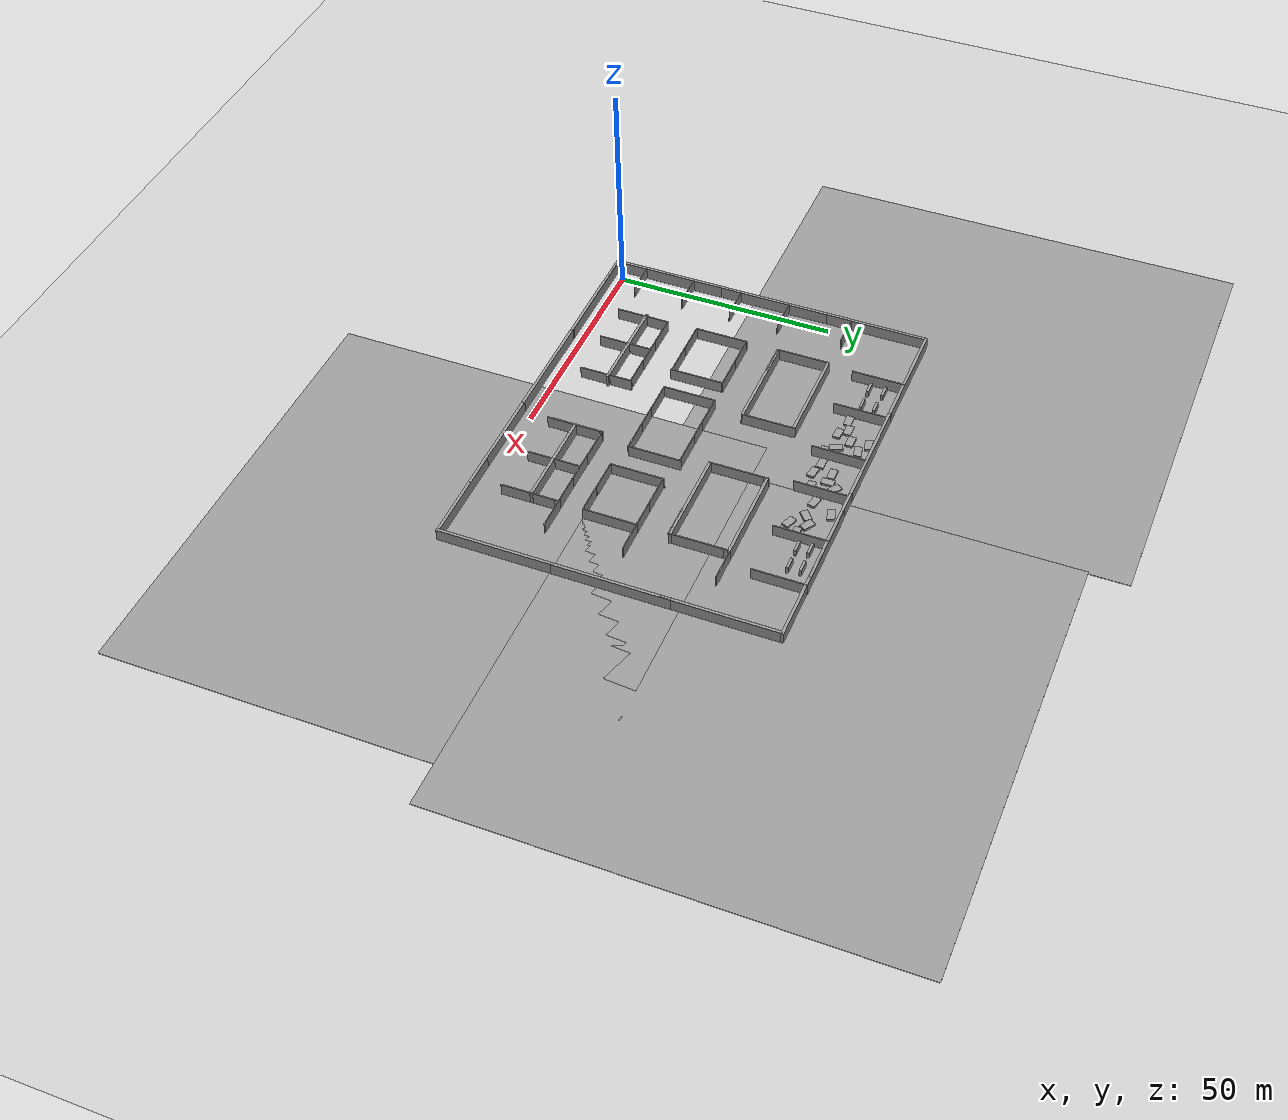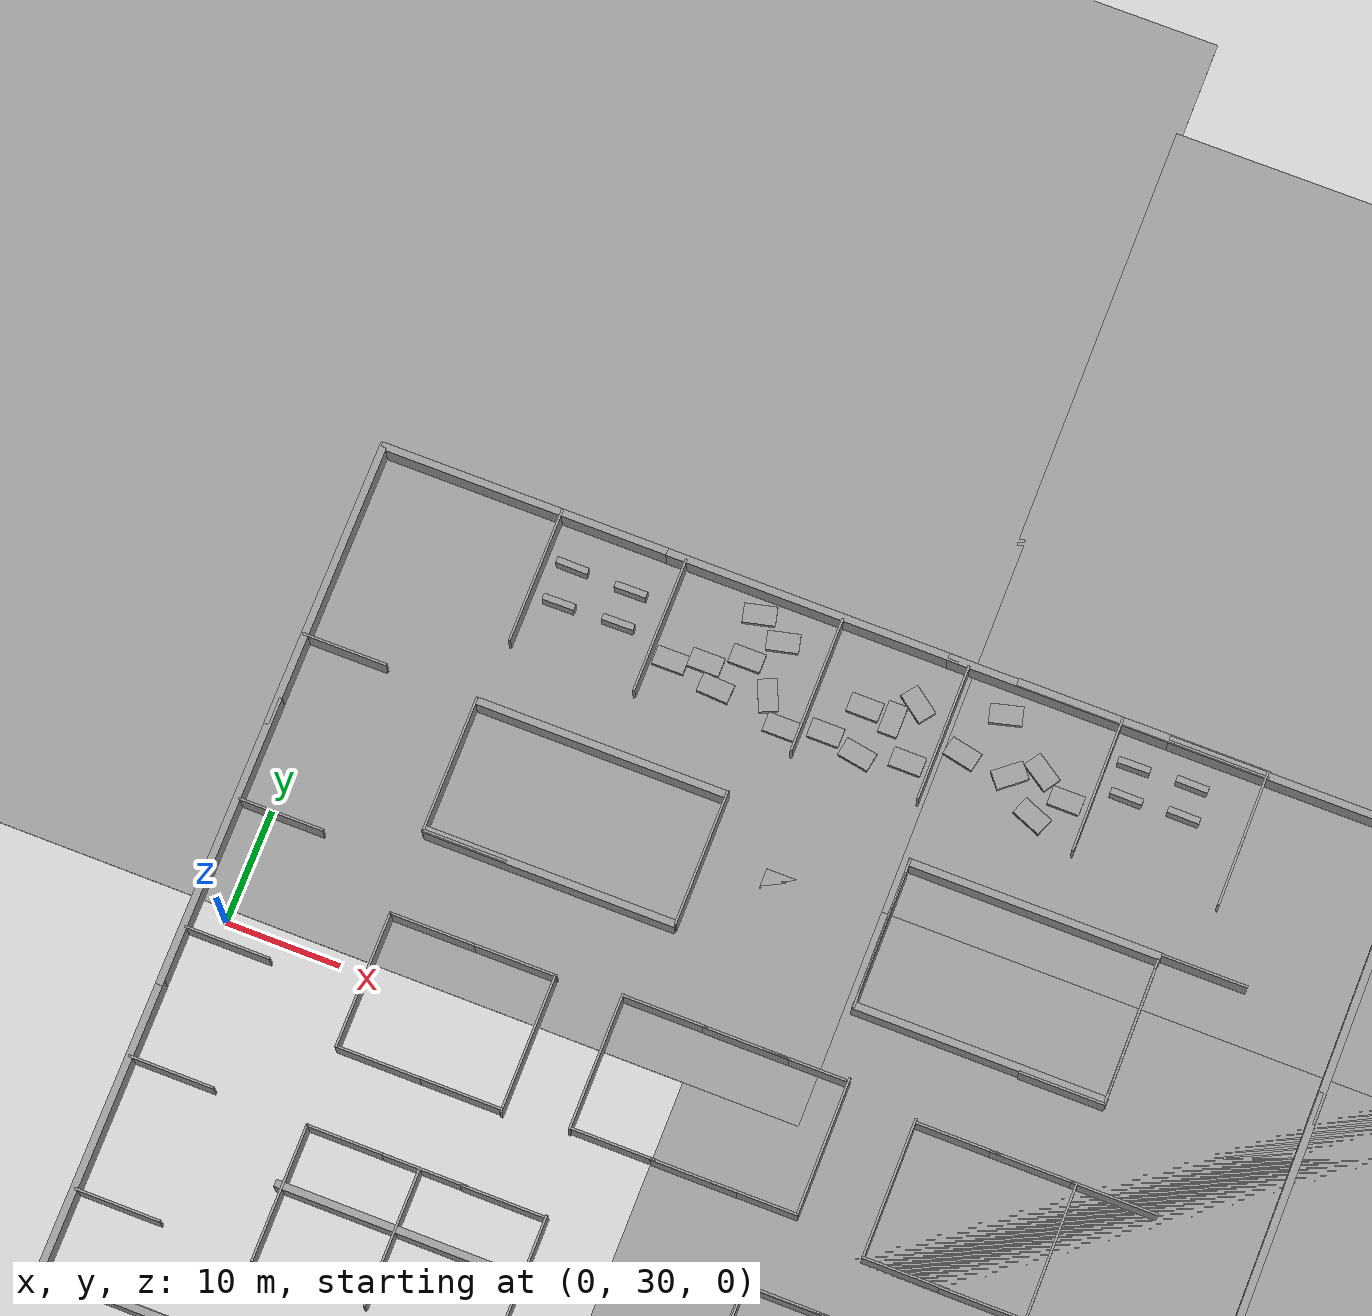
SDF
<sdf version="1.7">
 <world name="default">
  <light name="sun" type="directional">
   <pose>0 0 10 0 -0 0</pose>
   <diffuse>0.8 0.8 0.8 1</diffuse>
   <specular>0.2 0.2 0.2 1</specular>
   <attenuation>
    <range>1000</range>
    <constant>0.9</constant>
    <linear>0.01</linear>
    <quadratic>0.001</quadratic>
   </attenuation>
   <direction>-0.5 0.1 -0.9</direction>
   <spot><inner_angle>0</inner_angle><outer_angle>0</outer_angle><falloff>0</falloff></spot>
  </light>
  <plugin name="ros_interface_plugin" filename="librotors_gazebo_ros_interface_plugin.so"/>
  <plugin name="gazebo_ros_state" filename="libgazebo_ros_state.so"/>
  <model name="ground_plane">
   <static>1</static>
   <link name="link">
    <collision name="collision_collision">
     <geometry><plane><normal>0 0 1</normal><size>100 100</size></plane></geometry>
     <surface><friction><ode><mu>100</mu><mu2>50</mu2></ode></friction></surface>
    </collision>
    <visual name="visual">
     <cast_shadows>0</cast_shadows>
     <geometry><plane><normal>0 0 1</normal><size>100 100</size></plane></geometry>
     <material>
      <script><uri>file://media/materials/scripts/gazebo.material</uri><name>Gazebo/Grey</name></script>
     </material>
    </visual>
   </link>
  </model>
  <gravity>0 0 -9.81</gravity>
  <magnetic_field>6e-06 2.3e-05 -4.2e-05</magnetic_field>
  <atmosphere type="adiabatic"/>
  <physics name="default_physics" default="0" type="ode">
   <max_step_size>0.001</max_step_size>
   <real_time_factor>1</real_time_factor>
   <real_time_update_rate>1000</real_time_update_rate>
  </physics>
  <scene><ambient>0.4 0.4 0.4 1</ambient><background>0.7 0.7 0.7 1</background><shadows>1</shadows></scene>
  <spherical_coordinates>
   <surface_model>EARTH_WGS84</surface_model>
   <latitude_deg>0</latitude_deg>
   <longitude_deg>0</longitude_deg>
   <elevation>0</elevation>
   <heading_deg>0</heading_deg>
  </spherical_coordinates>
  <model name="grey_wall_long">
   <link name="link">
    <pose>0 0 1.37589 0 -0 0</pose>
    <inertial>
     <inertia><ixx>0</ixx><ixy>0</ixy><ixz>0</ixz><iyy>0</iyy><iyz>0</iyz><izz>0</izz></inertia>
     <mass>0</mass>
    </inertial>
    <visual name="visual">
     <cast_shadows>0</cast_shadows>
     <geometry><box><size>25.8815 0.642976 2.8</size></box></geometry>
     <material>
      <script>
       <uri>model://grey_wall/materials/scripts</uri>
       <uri>model://grey_wall/materials/textures</uri>
       <name>vrc/grey_wall</name>
      </script>
      <shader type="pixel"><normal_map>__default__</normal_map></shader>
      <ambient>1 1 1 1</ambient>
      <diffuse>1 1 1 1</diffuse>
      <specular>0 0 0 1</specular>
      <emissive>0 0 0 1</emissive>
     </material>
    </visual>
    <collision name="collision_collision">
     <geometry><box><size>25.8815 0.642976 2.8</size></box></geometry>
     <surface>
      <friction>
       <ode><mu>1</mu><mu2>1</mu2><fdir1>0 0 0</fdir1><slip1>0</slip1><slip2>0</slip2></ode>
       <torsional>
        <coefficient>1</coefficient>
        <patch_radius>0</patch_radius>
        <surface_radius>0</surface_radius>
        <use_patch_radius>1</use_patch_radius>
        <ode><slip>0</slip></ode>
       </torsional>
      </friction>
      <bounce><restitution_coefficient>0</restitution_coefficient><threshold>1e+06</threshold></bounce>
      <contact>
       <collide_without_contact>0</collide_without_contact>
       <collide_without_contact_bitmask>1</collide_without_contact_bitmask>
       <collide_bitmask>1</collide_bitmask>
       <ode>
        <soft_cfm>0</soft_cfm>
        <soft_erp>0.2</soft_erp>
        <kp>1e+13</kp>
        <kd>1</kd>
        <max_vel>0.01</max_vel>
        <min_depth>0</min_depth>
       </ode>
       <bullet>
        <split_impulse>1</split_impulse>
        <split_impulse_penetration_threshold>-0.01</split_impulse_penetration_threshold>
        <soft_cfm>0</soft_cfm>
        <soft_erp>0.2</soft_erp>
        <kp>1e+13</kp>
        <kd>1</kd>
       </bullet>
      </contact>
     </surface>
    </collision>
   </link>
   <static>1</static>
   <pose>10.3524 -2.38269 0 0 -0 0</pose>
  </model>
  <model name="grey_wall_long_0">
   <link name="link">
    <pose>0 0 1.37589 0 -0 0</pose>
    <inertial>
     <inertia><ixx>0</ixx><ixy>0</ixy><ixz>0</ixz><iyy>0</iyy><iyz>0</iyz><izz>0</izz></inertia>
     <mass>0</mass>
    </inertial>
    <visual name="visual">
     <cast_shadows>0</cast_shadows>
     <geometry><box><size>25.8815 0.642976 2.8</size></box></geometry>
     <material>
      <script>
       <uri>model://grey_wall/materials/scripts</uri>
       <uri>model://grey_wall/materials/textures</uri>
       <name>vrc/grey_wall</name>
      </script>
      <shader type="pixel"><normal_map>__default__</normal_map></shader>
      <ambient>1 1 1 1</ambient>
      <diffuse>1 1 1 1</diffuse>
      <specular>0 0 0 1</specular>
      <emissive>0 0 0 1</emissive>
     </material>
    </visual>
    <collision name="collision_collision">
     <geometry><box><size>25.8815 0.642976 2.8</size></box></geometry>
     <surface>
      <friction>
       <ode><mu>1</mu><mu2>1</mu2><fdir1>0 0 0</fdir1><slip1>0</slip1><slip2>0</slip2></ode>
       <torsional>
        <coefficient>1</coefficient>
        <patch_radius>0</patch_radius>
        <surface_radius>0</surface_radius>
        <use_patch_radius>1</use_patch_radius>
        <ode><slip>0</slip></ode>
       </torsional>
      </friction>
      <bounce><restitution_coefficient>0</restitution_coefficient><threshold>1e+06</threshold></bounce>
      <contact>
       <collide_without_contact>0</collide_without_contact>
       <collide_without_contact_bitmask>1</collide_without_contact_bitmask>
       <collide_bitmask>1</collide_bitmask>
       <ode>
        <soft_cfm>0</soft_cfm>
        <soft_erp>0.2</soft_erp>
        <kp>1e+13</kp>
        <kd>1</kd>
        <max_vel>0.01</max_vel>
        <min_depth>0</min_depth>
       </ode>
       <bullet>
        <split_impulse>1</split_impulse>
        <split_impulse_penetration_threshold>-0.01</split_impulse_penetration_threshold>
        <soft_cfm>0</soft_cfm>
        <soft_erp>0.2</soft_erp>
        <kp>1e+13</kp>
        <kd>1</kd>
       </bullet>
      </contact>
     </surface>
    </collision>
   </link>
   <static>1</static>
   <pose>35.9605 -2.39418 0 0 -0 0</pose>
  </model>
  <model name="grey_wall_long_1">
   <link name="link">
    <pose>0 0 1.37589 0 -0 0</pose>
    <inertial>
     <inertia><ixx>0</ixx><ixy>0</ixy><ixz>0</ixz><iyy>0</iyy><iyz>0</iyz><izz>0</izz></inertia>
     <mass>0</mass>
    </inertial>
    <visual name="visual">
     <cast_shadows>0</cast_shadows>
     <geometry><box><size>25.8815 0.642976 2.8</size></box></geometry>
     <material>
      <script>
       <uri>model://grey_wall/materials/scripts</uri>
       <uri>model://grey_wall/materials/textures</uri>
       <name>vrc/grey_wall</name>
      </script>
      <shader type="pixel"><normal_map>__default__</normal_map></shader>
      <ambient>1 1 1 1</ambient>
      <diffuse>1 1 1 1</diffuse>
      <specular>0 0 0 1</specular>
      <emissive>0 0 0 1</emissive>
     </material>
    </visual>
    <collision name="collision_collision">
     <geometry><box><size>25.8815 0.642976 2.8</size></box></geometry>
     <surface>
      <friction>
       <ode><mu>1</mu><mu2>1</mu2><fdir1>0 0 0</fdir1><slip1>0</slip1><slip2>0</slip2></ode>
       <torsional>
        <coefficient>1</coefficient>
        <patch_radius>0</patch_radius>
        <surface_radius>0</surface_radius>
        <use_patch_radius>1</use_patch_radius>
        <ode><slip>0</slip></ode>
       </torsional>
      </friction>
      <bounce><restitution_coefficient>0</restitution_coefficient><threshold>1e+06</threshold></bounce>
      <contact>
       <collide_without_contact>0</collide_without_contact>
       <collide_without_contact_bitmask>1</collide_without_contact_bitmask>
       <collide_bitmask>1</collide_bitmask>
       <ode>
        <soft_cfm>0</soft_cfm>
        <soft_erp>0.2</soft_erp>
        <kp>1e+13</kp>
        <kd>1</kd>
        <max_vel>0.01</max_vel>
        <min_depth>0</min_depth>
       </ode>
       <bullet>
        <split_impulse>1</split_impulse>
        <split_impulse_penetration_threshold>-0.01</split_impulse_penetration_threshold>
        <soft_cfm>0</soft_cfm>
        <soft_erp>0.2</soft_erp>
        <kp>1e+13</kp>
        <kd>1</kd>
       </bullet>
      </contact>
     </surface>
    </collision>
   </link>
   <static>1</static>
   <pose>61.3257 -2.37865 0 0 -0 0</pose>
  </model>
  <model name="ground_plane_0">
   <static>1</static>
   <link name="link">
    <collision name="collision_collision">
     <geometry><plane><normal>0 0 1</normal><size>100 100</size></plane></geometry>
     <surface><friction><ode><mu>100</mu><mu2>50</mu2></ode></friction></surface>
    </collision>
    <visual name="visual">
     <cast_shadows>0</cast_shadows>
     <geometry><plane><normal>0 0 1</normal><size>100 100</size></plane></geometry>
     <material>
      <script><uri>file://media/materials/scripts/gazebo.material</uri><name>Gazebo/Grey</name></script>
     </material>
    </visual>
   </link>
   <pose>-0.073857 81.0851 0 0 -0 0</pose>
  </model>
  <model name="ground_plane_1">
   <static>1</static>
   <link name="link">
    <collision name="collision_collision">
     <geometry><plane><normal>0 0 1</normal><size>100 100</size></plane></geometry>
     <surface><friction><ode><mu>100</mu><mu2>50</mu2></ode></friction></surface>
    </collision>
    <visual name="visual">
     <cast_shadows>0</cast_shadows>
     <geometry><plane><normal>0 0 1</normal><size>100 100</size></plane></geometry>
     <material>
      <script><uri>file://media/materials/scripts/gazebo.material</uri><name>Gazebo/Grey</name></script>
     </material>
    </visual>
   </link>
   <pose>89.798 0.232818 0 0 -0 0</pose>
  </model>
  <model name="ground_plane_2">
   <static>1</static>
   <link name="link">
    <collision name="collision_collision">
     <geometry><plane><normal>0 0 1</normal><size>100 100</size></plane></geometry>
     <surface><friction><ode><mu>100</mu><mu2>50</mu2></ode></friction></surface>
    </collision>
    <visual name="visual">
     <cast_shadows>0</cast_shadows>
     <geometry><plane><normal>0 0 1</normal><size>100 100</size></plane></geometry>
     <material>
      <script><uri>file://media/materials/scripts/gazebo.material</uri><name>Gazebo/Grey</name></script>
     </material>
    </visual>
   </link>
   <pose>99.3631 72.3911 0 0 -0 0</pose>
  </model>
  <model name="grew_wall_long_vertial_0_clone">
   <model name="grey_wall_long">
    <link name="link">
     <pose>0 0 1.37589 0 -0 0</pose>
     <inertial>
      <inertia><ixx>0</ixx><ixy>0</ixy><ixz>0</ixz><iyy>0</iyy><iyz>0</iyz><izz>0</izz></inertia>
      <mass>0</mass>
     </inertial>
     <visual name="visual">
      <cast_shadows>0</cast_shadows>
      <geometry><box><size>25.8815 0.642976 2.8</size></box></geometry>
      <material>
       <script>
        <uri>model://grey_wall/materials/scripts</uri>
        <uri>model://grey_wall/materials/textures</uri>
        <name>vrc/grey_wall</name>
       </script>
       <shader type="pixel"><normal_map>__default__</normal_map></shader>
       <ambient>1 1 1 1</ambient>
       <diffuse>1 1 1 1</diffuse>
       <specular>0 0 0 1</specular>
       <emissive>0 0 0 1</emissive>
      </material>
     </visual>
     <collision name="collision_collision">
      <geometry><box><size>25.8815 0.642976 2.8</size></box></geometry>
      <surface>
       <friction>
        <ode><mu>1</mu><mu2>1</mu2><fdir1>0 0 0</fdir1><slip1>0</slip1><slip2>0</slip2></ode>
        <torsional>
         <coefficient>1</coefficient>
         <patch_radius>0</patch_radius>
         <surface_radius>0</surface_radius>
         <use_patch_radius>1</use_patch_radius>
         <ode><slip>0</slip></ode>
        </torsional>
       </friction>
       <bounce><restitution_coefficient>0</restitution_coefficient><threshold>1e+06</threshold></bounce>
       <contact>
        <collide_without_contact>0</collide_without_contact>
        <collide_without_contact_bitmask>1</collide_without_contact_bitmask>
        <collide_bitmask>1</collide_bitmask>
        <ode>
         <soft_cfm>0</soft_cfm>
         <soft_erp>0.2</soft_erp>
         <kp>1e+13</kp>
         <kd>1</kd>
         <max_vel>0.01</max_vel>
         <min_depth>0</min_depth>
        </ode>
        <bullet>
         <split_impulse>1</split_impulse>
         <split_impulse_penetration_threshold>-0.01</split_impulse_penetration_threshold>
         <soft_cfm>0</soft_cfm>
         <soft_erp>0.2</soft_erp>
         <kp>1e+13</kp>
         <kd>1</kd>
        </bullet>
       </contact>
      </surface>
     </collision>
    </link>
    <static>1</static>
    <pose>1e-06 -0 0 0 -0 1.57003</pose>
   </model>
   <static>0</static>
   <pose>-2.80084 59.1647 0 0 -0 0</pose>
  </model>
  <model name="grey_wall_long_term">
   <link name="link">
    <pose>-1.74587 -0.378849 1.37589 0 -0 0</pose>
    <inertial>
     <inertia><ixx>0</ixx><ixy>0</ixy><ixz>0</ixz><iyy>0</iyy><iyz>0</iyz><izz>0</izz></inertia>
     <mass>0</mass>
    </inertial>
    <visual name="visual">
     <cast_shadows>0</cast_shadows>
     <geometry><box><size>22.1596 0.642976 2.8</size></box></geometry>
     <material>
      <script>
       <uri>model://grey_wall/materials/scripts</uri>
       <uri>model://grey_wall/materials/textures</uri>
       <name>vrc/grey_wall</name>
      </script>
      <shader type="pixel"><normal_map>__default__</normal_map></shader>
      <ambient>1 1 1 1</ambient>
      <diffuse>1 1 1 1</diffuse>
      <specular>0 0 0 1</specular>
      <emissive>0 0 0 1</emissive>
     </material>
    </visual>
    <collision name="collision_collision">
     <geometry><box><size>22.1596 0.642976 2.8</size></box></geometry>
     <surface>
      <friction>
       <ode><mu>1</mu><mu2>1</mu2><fdir1>0 0 0</fdir1><slip1>0</slip1><slip2>0</slip2></ode>
       <torsional>
        <coefficient>1</coefficient>
        <patch_radius>0</patch_radius>
        <surface_radius>0</surface_radius>
        <use_patch_radius>1</use_patch_radius>
        <ode><slip>0</slip></ode>
       </torsional>
      </friction>
      <bounce><restitution_coefficient>0</restitution_coefficient><threshold>1e+06</threshold></bounce>
      <contact>
       <collide_without_contact>0</collide_without_contact>
       <collide_without_contact_bitmask>1</collide_without_contact_bitmask>
       <collide_bitmask>1</collide_bitmask>
       <ode>
        <soft_cfm>0</soft_cfm>
        <soft_erp>0.2</soft_erp>
        <kp>1e+13</kp>
        <kd>1</kd>
        <max_vel>0.01</max_vel>
        <min_depth>0</min_depth>
       </ode>
       <bullet>
        <split_impulse>1</split_impulse>
        <split_impulse_penetration_threshold>-0.01</split_impulse_penetration_threshold>
        <soft_cfm>0</soft_cfm>
        <soft_erp>0.2</soft_erp>
        <kp>1e+13</kp>
        <kd>1</kd>
       </bullet>
      </contact>
     </surface>
    </collision>
   </link>
   <static>1</static>
   <pose>25.4016 54.6879 0 0 -0 0</pose>
  </model>
  <model name="grey_wall_long_2_clone">
   <link name="link">
    <pose>0 0 1.37589 0 -0 0</pose>
    <inertial>
     <inertia><ixx>0</ixx><ixy>0</ixy><ixz>0</ixz><iyy>0</iyy><iyz>0</iyz><izz>0</izz></inertia>
     <mass>0</mass>
    </inertial>
    <visual name="visual">
     <cast_shadows>0</cast_shadows>
     <geometry><box><size>25.8815 0.642976 2.8</size></box></geometry>
     <material>
      <script>
       <uri>model://grey_wall/materials/scripts</uri>
       <uri>model://grey_wall/materials/textures</uri>
       <name>vrc/grey_wall</name>
      </script>
      <shader type="pixel"><normal_map>__default__</normal_map></shader>
      <ambient>1 1 1 1</ambient>
      <diffuse>1 1 1 1</diffuse>
      <specular>0 0 0 1</specular>
      <emissive>0 0 0 1</emissive>
     </material>
    </visual>
    <collision name="collision_collision">
     <geometry><box><size>25.8815 0.642976 2.8</size></box></geometry>
     <surface>
      <friction>
       <ode><mu>1</mu><mu2>1</mu2><fdir1>0 0 0</fdir1><slip1>0</slip1><slip2>0</slip2></ode>
       <torsional>
        <coefficient>1</coefficient>
        <patch_radius>0</patch_radius>
        <surface_radius>0</surface_radius>
        <use_patch_radius>1</use_patch_radius>
        <ode><slip>0</slip></ode>
       </torsional>
      </friction>
      <bounce><restitution_coefficient>0</restitution_coefficient><threshold>1e+06</threshold></bounce>
      <contact>
       <collide_without_contact>0</collide_without_contact>
       <collide_without_contact_bitmask>1</collide_without_contact_bitmask>
       <collide_bitmask>1</collide_bitmask>
       <ode>
        <soft_cfm>0</soft_cfm>
        <soft_erp>0.2</soft_erp>
        <kp>1e+13</kp>
        <kd>1</kd>
        <max_vel>0.01</max_vel>
        <min_depth>0</min_depth>
       </ode>
       <bullet>
        <split_impulse>1</split_impulse>
        <split_impulse_penetration_threshold>-0.01</split_impulse_penetration_threshold>
        <soft_cfm>0</soft_cfm>
        <soft_erp>0.2</soft_erp>
        <kp>1e+13</kp>
        <kd>1</kd>
       </bullet>
      </contact>
     </surface>
    </collision>
   </link>
   <static>1</static>
   <pose>35.559 71.815 0 0 -0 0</pose>
  </model>
  <model name="grey_wall_long_2_clone_0">
   <link name="link">
    <pose>0 0 1.37589 0 -0 0</pose>
    <inertial>
     <inertia><ixx>0</ixx><ixy>0</ixy><ixz>0</ixz><iyy>0</iyy><iyz>0</iyz><izz>0</izz></inertia>
     <mass>0</mass>
    </inertial>
    <visual name="visual">
     <cast_shadows>0</cast_shadows>
     <geometry><box><size>25.8815 0.642976 2.8</size></box></geometry>
     <material>
      <script>
       <uri>model://grey_wall/materials/scripts</uri>
       <uri>model://grey_wall/materials/textures</uri>
       <name>vrc/grey_wall</name>
      </script>
      <shader type="pixel"><normal_map>__default__</normal_map></shader>
      <ambient>1 1 1 1</ambient>
      <diffuse>1 1 1 1</diffuse>
      <specular>0 0 0 1</specular>
      <emissive>0 0 0 1</emissive>
     </material>
    </visual>
    <collision name="collision_collision">
     <geometry><box><size>25.8815 0.642976 2.8</size></box></geometry>
     <surface>
      <friction>
       <ode><mu>1</mu><mu2>1</mu2><fdir1>0 0 0</fdir1><slip1>0</slip1><slip2>0</slip2></ode>
       <torsional>
        <coefficient>1</coefficient>
        <patch_radius>0</patch_radius>
        <surface_radius>0</surface_radius>
        <use_patch_radius>1</use_patch_radius>
        <ode><slip>0</slip></ode>
       </torsional>
      </friction>
      <bounce><restitution_coefficient>0</restitution_coefficient><threshold>1e+06</threshold></bounce>
      <contact>
       <collide_without_contact>0</collide_without_contact>
       <collide_without_contact_bitmask>1</collide_without_contact_bitmask>
       <collide_bitmask>1</collide_bitmask>
       <ode>
        <soft_cfm>0</soft_cfm>
        <soft_erp>0.2</soft_erp>
        <kp>1e+13</kp>
        <kd>1</kd>
        <max_vel>0.01</max_vel>
        <min_depth>0</min_depth>
       </ode>
       <bullet>
        <split_impulse>1</split_impulse>
        <split_impulse_penetration_threshold>-0.01</split_impulse_penetration_threshold>
        <soft_cfm>0</soft_cfm>
        <soft_erp>0.2</soft_erp>
        <kp>1e+13</kp>
        <kd>1</kd>
       </bullet>
      </contact>
     </surface>
    </collision>
   </link>
   <static>1</static>
   <pose>60.5181 71.8016 0 0 -0 0</pose>
  </model>
  <model name="grey_wall_long_term_clone_0">
   <link name="link">
    <pose>-1.74587 -0.378849 1.37589 0 -0 0</pose>
    <inertial>
     <inertia><ixx>0</ixx><ixy>0</ixy><ixz>0</ixz><iyy>0</iyy><iyz>0</iyz><izz>0</izz></inertia>
     <mass>0</mass>
    </inertial>
    <visual name="visual">
     <cast_shadows>0</cast_shadows>
     <geometry><box><size>22.1596 0.642976 2.8</size></box></geometry>
     <material>
      <script>
       <uri>model://grey_wall/materials/scripts</uri>
       <uri>model://grey_wall/materials/textures</uri>
       <name>vrc/grey_wall</name>
      </script>
      <shader type="pixel"><normal_map>__default__</normal_map></shader>
      <ambient>1 1 1 1</ambient>
      <diffuse>1 1 1 1</diffuse>
      <specular>0 0 0 1</specular>
      <emissive>0 0 0 1</emissive>
     </material>
    </visual>
    <collision name="collision_collision">
     <geometry><box><size>22.1596 0.642976 2.8</size></box></geometry>
     <surface>
      <friction>
       <ode><mu>1</mu><mu2>1</mu2><fdir1>0 0 0</fdir1><slip1>0</slip1><slip2>0</slip2></ode>
       <torsional>
        <coefficient>1</coefficient>
        <patch_radius>0</patch_radius>
        <surface_radius>0</surface_radius>
        <use_patch_radius>1</use_patch_radius>
        <ode><slip>0</slip></ode>
       </torsional>
      </friction>
      <bounce><restitution_coefficient>0</restitution_coefficient><threshold>1e+06</threshold></bounce>
      <contact>
       <collide_without_contact>0</collide_without_contact>
       <collide_without_contact_bitmask>1</collide_without_contact_bitmask>
       <collide_bitmask>1</collide_bitmask>
       <ode>
        <soft_cfm>0</soft_cfm>
        <soft_erp>0.2</soft_erp>
        <kp>1e+13</kp>
        <kd>1</kd>
        <max_vel>0.01</max_vel>
        <min_depth>0</min_depth>
       </ode>
       <bullet>
        <split_impulse>1</split_impulse>
        <split_impulse_penetration_threshold>-0.01</split_impulse_penetration_threshold>
        <soft_cfm>0</soft_cfm>
        <soft_erp>0.2</soft_erp>
        <kp>1e+13</kp>
        <kd>1</kd>
       </bullet>
      </contact>
     </surface>
    </collision>
   </link>
   <static>1</static>
   <pose>63.4001 54.7813 0 0 -0 0</pose>
  </model>
  <model name="grew_wall_long_vertial_1_clone_clone_1_clone">
   <model name="grey_wall_long">
    <link name="link">
     <pose>0 0 1.37589 0 -0 0</pose>
     <inertial>
      <inertia><ixx>0</ixx><ixy>0</ixy><ixz>0</ixz><iyy>0</iyy><iyz>0</iyz><izz>0</izz></inertia>
      <mass>0</mass>
     </inertial>
     <visual name="visual">
      <cast_shadows>0</cast_shadows>
      <geometry><box><size>25.8815 0.642976 2.8</size></box></geometry>
      <material>
       <script>
        <uri>model://grey_wall/materials/scripts</uri>
        <uri>model://grey_wall/materials/textures</uri>
        <name>vrc/grey_wall</name>
       </script>
       <shader type="pixel"><normal_map>__default__</normal_map></shader>
       <ambient>1 1 1 1</ambient>
       <diffuse>1 1 1 1</diffuse>
       <specular>0 0 0 1</specular>
       <emissive>0 0 0 1</emissive>
      </material>
     </visual>
     <collision name="collision_collision">
      <geometry><box><size>25.8815 0.642976 2.8</size></box></geometry>
      <surface>
       <friction>
        <ode><mu>1</mu><mu2>1</mu2><fdir1>0 0 0</fdir1><slip1>0</slip1><slip2>0</slip2></ode>
        <torsional>
         <coefficient>1</coefficient>
         <patch_radius>0</patch_radius>
         <surface_radius>0</surface_radius>
         <use_patch_radius>1</use_patch_radius>
         <ode><slip>0</slip></ode>
        </torsional>
       </friction>
       <bounce><restitution_coefficient>0</restitution_coefficient><threshold>1e+06</threshold></bounce>
       <contact>
        <collide_without_contact>0</collide_without_contact>
        <collide_without_contact_bitmask>1</collide_without_contact_bitmask>
        <collide_bitmask>1</collide_bitmask>
        <ode>
         <soft_cfm>0</soft_cfm>
         <soft_erp>0.2</soft_erp>
         <kp>1e+13</kp>
         <kd>1</kd>
         <max_vel>0.01</max_vel>
         <min_depth>0</min_depth>
        </ode>
        <bullet>
         <split_impulse>1</split_impulse>
         <split_impulse_penetration_threshold>-0.01</split_impulse_penetration_threshold>
         <soft_cfm>0</soft_cfm>
         <soft_erp>0.2</soft_erp>
         <kp>1e+13</kp>
         <kd>1</kd>
        </bullet>
       </contact>
      </surface>
     </collision>
    </link>
    <static>1</static>
    <pose>1e-06 -0 0 0 -0 1.57003</pose>
   </model>
   <static>0</static>
   <pose>88.7842 10.2506 0 0 -0 0</pose>
  </model>
  <model name="grew_wall_long_vertial_1_clone_clone_1_clone_0">
   <model name="grey_wall_long">
    <link name="link">
     <pose>0 0 1.37589 0 -0 0</pose>
     <inertial>
      <inertia><ixx>0</ixx><ixy>0</ixy><ixz>0</ixz><iyy>0</iyy><iyz>0</iyz><izz>0</izz></inertia>
      <mass>0</mass>
     </inertial>
     <visual name="visual">
      <cast_shadows>0</cast_shadows>
      <geometry><box><size>25.8815 0.642976 2.8</size></box></geometry>
      <material>
       <script>
        <uri>model://grey_wall/materials/scripts</uri>
        <uri>model://grey_wall/materials/textures</uri>
        <name>vrc/grey_wall</name>
       </script>
       <shader type="pixel"><normal_map>__default__</normal_map></shader>
       <ambient>1 1 1 1</ambient>
       <diffuse>1 1 1 1</diffuse>
       <specular>0 0 0 1</specular>
       <emissive>0 0 0 1</emissive>
      </material>
     </visual>
     <collision name="collision_collision">
      <geometry><box><size>25.8815 0.642976 2.8</size></box></geometry>
      <surface>
       <friction>
        <ode><mu>1</mu><mu2>1</mu2><fdir1>0 0 0</fdir1><slip1>0</slip1><slip2>0</slip2></ode>
        <torsional>
         <coefficient>1</coefficient>
         <patch_radius>0</patch_radius>
         <surface_radius>0</surface_radius>
         <use_patch_radius>1</use_patch_radius>
         <ode><slip>0</slip></ode>
        </torsional>
       </friction>
       <bounce><restitution_coefficient>0</restitution_coefficient><threshold>1e+06</threshold></bounce>
       <contact>
        <collide_without_contact>0</collide_without_contact>
        <collide_without_contact_bitmask>1</collide_without_contact_bitmask>
        <collide_bitmask>1</collide_bitmask>
        <ode>
         <soft_cfm>0</soft_cfm>
         <soft_erp>0.2</soft_erp>
         <kp>1e+13</kp>
         <kd>1</kd>
         <max_vel>0.01</max_vel>
         <min_depth>0</min_depth>
        </ode>
        <bullet>
         <split_impulse>1</split_impulse>
         <split_impulse_penetration_threshold>-0.01</split_impulse_penetration_threshold>
         <soft_cfm>0</soft_cfm>
         <soft_erp>0.2</soft_erp>
         <kp>1e+13</kp>
         <kd>1</kd>
        </bullet>
       </contact>
      </surface>
     </collision>
    </link>
    <static>1</static>
    <pose>1e-06 -0 0 0 -0 1.57003</pose>
   </model>
   <static>0</static>
   <pose>88.8179 35.6019 0 0 -0 0</pose>
  </model>
  <model name="grew_wall_long_vertial_1_clone_clone_1_clone_1">
   <model name="grey_wall_long">
    <link name="link">
     <pose>0 0 1.37589 0 -0 0</pose>
     <inertial>
      <inertia><ixx>0</ixx><ixy>0</ixy><ixz>0</ixz><iyy>0</iyy><iyz>0</iyz><izz>0</izz></inertia>
      <mass>0</mass>
     </inertial>
     <visual name="visual">
      <cast_shadows>0</cast_shadows>
      <geometry><box><size>25.8815 0.642976 2.8</size></box></geometry>
      <material>
       <script>
        <uri>model://grey_wall/materials/scripts</uri>
        <uri>model://grey_wall/materials/textures</uri>
        <name>vrc/grey_wall</name>
       </script>
       <shader type="pixel"><normal_map>__default__</normal_map></shader>
       <ambient>1 1 1 1</ambient>
       <diffuse>1 1 1 1</diffuse>
       <specular>0 0 0 1</specular>
       <emissive>0 0 0 1</emissive>
      </material>
     </visual>
     <collision name="collision_collision">
      <geometry><box><size>25.8815 0.642976 2.8</size></box></geometry>
      <surface>
       <friction>
        <ode><mu>1</mu><mu2>1</mu2><fdir1>0 0 0</fdir1><slip1>0</slip1><slip2>0</slip2></ode>
        <torsional>
         <coefficient>1</coefficient>
         <patch_radius>0</patch_radius>
         <surface_radius>0</surface_radius>
         <use_patch_radius>1</use_patch_radius>
         <ode><slip>0</slip></ode>
        </torsional>
       </friction>
       <bounce><restitution_coefficient>0</restitution_coefficient><threshold>1e+06</threshold></bounce>
       <contact>
        <collide_without_contact>0</collide_without_contact>
        <collide_without_contact_bitmask>1</collide_without_contact_bitmask>
        <collide_bitmask>1</collide_bitmask>
        <ode>
         <soft_cfm>0</soft_cfm>
         <soft_erp>0.2</soft_erp>
         <kp>1e+13</kp>
         <kd>1</kd>
         <max_vel>0.01</max_vel>
         <min_depth>0</min_depth>
        </ode>
        <bullet>
         <split_impulse>1</split_impulse>
         <split_impulse_penetration_threshold>-0.01</split_impulse_penetration_threshold>
         <soft_cfm>0</soft_cfm>
         <soft_erp>0.2</soft_erp>
         <kp>1e+13</kp>
         <kd>1</kd>
        </bullet>
       </contact>
      </surface>
     </collision>
    </link>
    <static>1</static>
    <pose>1e-06 -0 0 0 -0 1.57003</pose>
   </model>
   <static>0</static>
   <pose>88.8126 58.7743 0 0 -0 0</pose>
  </model>
  <model name="grey_wall_long_term_clone_0_clone">
   <link name="link">
    <pose>-1.74587 -0.378849 1.37589 0 -0 0</pose>
    <inertial>
     <inertia><ixx>0</ixx><ixy>0</ixy><ixz>0</ixz><iyy>0</iyy><iyz>0</iyz><izz>0</izz></inertia>
     <mass>0</mass>
    </inertial>
    <visual name="visual">
     <cast_shadows>0</cast_shadows>
     <geometry><box><size>22.1596 0.642976 2.8</size></box></geometry>
     <material>
      <script>
       <uri>model://grey_wall/materials/scripts</uri>
       <uri>model://grey_wall/materials/textures</uri>
       <name>vrc/grey_wall</name>
      </script>
      <shader type="pixel"><normal_map>__default__</normal_map></shader>
      <ambient>1 1 1 1</ambient>
      <diffuse>1 1 1 1</diffuse>
      <specular>0 0 0 1</specular>
      <emissive>0 0 0 1</emissive>
     </material>
    </visual>
    <collision name="collision_collision">
     <geometry><box><size>22.1596 0.642976 2.8</size></box></geometry>
     <surface>
      <friction>
       <ode><mu>1</mu><mu2>1</mu2><fdir1>0 0 0</fdir1><slip1>0</slip1><slip2>0</slip2></ode>
       <torsional>
        <coefficient>1</coefficient>
        <patch_radius>0</patch_radius>
        <surface_radius>0</surface_radius>
        <use_patch_radius>1</use_patch_radius>
        <ode><slip>0</slip></ode>
       </torsional>
      </friction>
      <bounce><restitution_coefficient>0</restitution_coefficient><threshold>1e+06</threshold></bounce>
      <contact>
       <collide_without_contact>0</collide_without_contact>
       <collide_without_contact_bitmask>1</collide_without_contact_bitmask>
       <collide_bitmask>1</collide_bitmask>
       <ode>
        <soft_cfm>0</soft_cfm>
        <soft_erp>0.2</soft_erp>
        <kp>1e+13</kp>
        <kd>1</kd>
        <max_vel>0.01</max_vel>
        <min_depth>0</min_depth>
       </ode>
       <bullet>
        <split_impulse>1</split_impulse>
        <split_impulse_penetration_threshold>-0.01</split_impulse_penetration_threshold>
        <soft_cfm>0</soft_cfm>
        <soft_erp>0.2</soft_erp>
        <kp>1e+13</kp>
        <kd>1</kd>
       </bullet>
      </contact>
     </surface>
    </collision>
   </link>
   <static>1</static>
   <pose>79.8463 72.1693 0 0 -0 0</pose>
  </model>
  <model name="grey_wall_long_term_clone_0_clone_0">
   <link name="link">
    <pose>-1.74587 -0.378849 1.37589 0 -0 0</pose>
    <inertial>
     <inertia><ixx>0</ixx><ixy>0</ixy><ixz>0</ixz><iyy>0</iyy><iyz>0</iyz><izz>0</izz></inertia>
     <mass>0</mass>
    </inertial>
    <visual name="visual">
     <cast_shadows>0</cast_shadows>
     <geometry><box><size>22.1596 0.642976 2.8</size></box></geometry>
     <material>
      <script>
       <uri>model://grey_wall/materials/scripts</uri>
       <uri>model://grey_wall/materials/textures</uri>
       <name>vrc/grey_wall</name>
      </script>
      <shader type="pixel"><normal_map>__default__</normal_map></shader>
      <ambient>1 1 1 1</ambient>
      <diffuse>1 1 1 1</diffuse>
      <specular>0 0 0 1</specular>
      <emissive>0 0 0 1</emissive>
     </material>
    </visual>
    <collision name="collision_collision">
     <geometry><box><size>22.1596 0.642976 2.8</size></box></geometry>
     <surface>
      <friction>
       <ode><mu>1</mu><mu2>1</mu2><fdir1>0 0 0</fdir1><slip1>0</slip1><slip2>0</slip2></ode>
       <torsional>
        <coefficient>1</coefficient>
        <patch_radius>0</patch_radius>
        <surface_radius>0</surface_radius>
        <use_patch_radius>1</use_patch_radius>
        <ode><slip>0</slip></ode>
       </torsional>
      </friction>
      <bounce><restitution_coefficient>0</restitution_coefficient><threshold>1e+06</threshold></bounce>
      <contact>
       <collide_without_contact>0</collide_without_contact>
       <collide_without_contact_bitmask>1</collide_without_contact_bitmask>
       <collide_bitmask>1</collide_bitmask>
       <ode>
        <soft_cfm>0</soft_cfm>
        <soft_erp>0.2</soft_erp>
        <kp>1e+13</kp>
        <kd>1</kd>
        <max_vel>0.01</max_vel>
        <min_depth>0</min_depth>
       </ode>
       <bullet>
        <split_impulse>1</split_impulse>
        <split_impulse_penetration_threshold>-0.01</split_impulse_penetration_threshold>
        <soft_cfm>0</soft_cfm>
        <soft_erp>0.2</soft_erp>
        <kp>1e+13</kp>
        <kd>1</kd>
       </bullet>
      </contact>
     </surface>
    </collision>
   </link>
   <static>1</static>
   <pose>79.4268 -1.97771 0 0 -0 0</pose>
  </model>
  <model name="grey_wall_12m_vertial_2_clone_clone_0">
   <link name="link">
    <pose>0.289112 -0.003891 1.4 0 0 -1.5701</pose>
    <inertial>
     <inertia><ixx>0</ixx><ixy>0</ixy><ixz>0</ixz><iyy>0</iyy><iyz>0</iyz><izz>0</izz></inertia>
     <mass>0</mass>
    </inertial>
    <visual name="visual">
     <cast_shadows>0</cast_shadows>
     <geometry><box><size>12.0527 0.2 2.8</size></box></geometry>
     <material>
      <script>
       <uri>model://grey_wall/materials/scripts</uri>
       <uri>model://grey_wall/materials/textures</uri>
       <name>vrc/grey_wall</name>
      </script>
      <shader type="pixel"/>
      <ambient>1 1 1 1</ambient>
      <diffuse>1 1 1 1</diffuse>
      <specular>0 0 0 1</specular>
      <emissive>0 0 0 1</emissive>
     </material>
    </visual>
    <collision name="collision_collision">
     <geometry><box><size>12.0527 0.2 2.8</size></box></geometry>
     <surface>
      <friction>
       <ode><mu>1</mu><mu2>1</mu2><fdir1>0 0 0</fdir1><slip1>0</slip1><slip2>0</slip2></ode>
       <torsional>
        <coefficient>1</coefficient>
        <patch_radius>0</patch_radius>
        <surface_radius>0</surface_radius>
        <use_patch_radius>1</use_patch_radius>
        <ode><slip>0</slip></ode>
       </torsional>
      </friction>
      <bounce><restitution_coefficient>0</restitution_coefficient><threshold>1e+06</threshold></bounce>
      <contact>
       <collide_without_contact>0</collide_without_contact>
       <collide_without_contact_bitmask>1</collide_without_contact_bitmask>
       <collide_bitmask>1</collide_bitmask>
       <ode>
        <soft_cfm>0</soft_cfm>
        <soft_erp>0.2</soft_erp>
        <kp>1e+13</kp>
        <kd>1</kd>
        <max_vel>0.01</max_vel>
        <min_depth>0</min_depth>
       </ode>
       <bullet>
        <split_impulse>1</split_impulse>
        <split_impulse_penetration_threshold>-0.01</split_impulse_penetration_threshold>
        <soft_cfm>0</soft_cfm>
        <soft_erp>0.2</soft_erp>
        <kp>1e+13</kp>
        <kd>1</kd>
       </bullet>
      </contact>
     </surface>
    </collision>
   </link>
   <static>1</static>
   <pose>12.5451 10.5106 0 0 -0 0</pose>
  </model>
  <model name="grey_wall_12m_vertial_2_clone_clone_1">
   <link name="link">
    <pose>0.289112 -0.003891 1.4 0 0 -1.5701</pose>
    <inertial>
     <inertia><ixx>0</ixx><ixy>0</ixy><ixz>0</ixz><iyy>0</iyy><iyz>0</iyz><izz>0</izz></inertia>
     <mass>0</mass>
    </inertial>
    <visual name="visual">
     <cast_shadows>0</cast_shadows>
     <geometry><box><size>12.0527 0.2 2.8</size></box></geometry>
     <material>
      <script>
       <uri>model://grey_wall/materials/scripts</uri>
       <uri>model://grey_wall/materials/textures</uri>
       <name>vrc/grey_wall</name>
      </script>
      <shader type="pixel"/>
      <ambient>1 1 1 1</ambient>
      <diffuse>1 1 1 1</diffuse>
      <specular>0 0 0 1</specular>
      <emissive>0 0 0 1</emissive>
     </material>
    </visual>
    <collision name="collision_collision">
     <geometry><box><size>12.0527 0.2 2.8</size></box></geometry>
     <surface>
      <friction>
       <ode><mu>1</mu><mu2>1</mu2><fdir1>0 0 0</fdir1><slip1>0</slip1><slip2>0</slip2></ode>
       <torsional>
        <coefficient>1</coefficient>
        <patch_radius>0</patch_radius>
        <surface_radius>0</surface_radius>
        <use_patch_radius>1</use_patch_radius>
        <ode><slip>0</slip></ode>
       </torsional>
      </friction>
      <bounce><restitution_coefficient>0</restitution_coefficient><threshold>1e+06</threshold></bounce>
      <contact>
       <collide_without_contact>0</collide_without_contact>
       <collide_without_contact_bitmask>1</collide_without_contact_bitmask>
       <collide_bitmask>1</collide_bitmask>
       <ode>
        <soft_cfm>0</soft_cfm>
        <soft_erp>0.2</soft_erp>
        <kp>1e+13</kp>
        <kd>1</kd>
        <max_vel>0.01</max_vel>
        <min_depth>0</min_depth>
       </ode>
       <bullet>
        <split_impulse>1</split_impulse>
        <split_impulse_penetration_threshold>-0.01</split_impulse_penetration_threshold>
        <soft_cfm>0</soft_cfm>
        <soft_erp>0.2</soft_erp>
        <kp>1e+13</kp>
        <kd>1</kd>
       </bullet>
      </contact>
     </surface>
    </collision>
   </link>
   <static>1</static>
   <pose>12.22 48.5915 0 0 -0 0</pose>
  </model>
  <model name="grey_wall_12m_vertial_2_clone_clone_2">
   <link name="link">
    <pose>0.289112 -0.003891 1.4 0 0 -1.5701</pose>
    <inertial>
     <inertia><ixx>0</ixx><ixy>0</ixy><ixz>0</ixz><iyy>0</iyy><iyz>0</iyz><izz>0</izz></inertia>
     <mass>0</mass>
    </inertial>
    <visual name="visual">
     <cast_shadows>0</cast_shadows>
     <geometry><box><size>12.0527 0.2 2.8</size></box></geometry>
     <material>
      <script>
       <uri>model://grey_wall/materials/scripts</uri>
       <uri>model://grey_wall/materials/textures</uri>
       <name>vrc/grey_wall</name>
      </script>
      <shader type="pixel"/>
      <ambient>1 1 1 1</ambient>
      <diffuse>1 1 1 1</diffuse>
      <specular>0 0 0 1</specular>
      <emissive>0 0 0 1</emissive>
     </material>
    </visual>
    <collision name="collision_collision">
     <geometry><box><size>12.0527 0.2 2.8</size></box></geometry>
     <surface>
      <friction>
       <ode><mu>1</mu><mu2>1</mu2><fdir1>0 0 0</fdir1><slip1>0</slip1><slip2>0</slip2></ode>
       <torsional>
        <coefficient>1</coefficient>
        <patch_radius>0</patch_radius>
        <surface_radius>0</surface_radius>
        <use_patch_radius>1</use_patch_radius>
        <ode><slip>0</slip></ode>
       </torsional>
      </friction>
      <bounce><restitution_coefficient>0</restitution_coefficient><threshold>1e+06</threshold></bounce>
      <contact>
       <collide_without_contact>0</collide_without_contact>
       <collide_without_contact_bitmask>1</collide_without_contact_bitmask>
       <collide_bitmask>1</collide_bitmask>
       <ode>
        <soft_cfm>0</soft_cfm>
        <soft_erp>0.2</soft_erp>
        <kp>1e+13</kp>
        <kd>1</kd>
        <max_vel>0.01</max_vel>
        <min_depth>0</min_depth>
       </ode>
       <bullet>
        <split_impulse>1</split_impulse>
        <split_impulse_penetration_threshold>-0.01</split_impulse_penetration_threshold>
        <soft_cfm>0</soft_cfm>
        <soft_erp>0.2</soft_erp>
        <kp>1e+13</kp>
        <kd>1</kd>
       </bullet>
      </contact>
     </surface>
    </collision>
   </link>
   <static>1</static>
   <pose>12.3021 29.2356 0 0 -0 0</pose>
  </model>
  <model name="grey_wall_0_clone_clone_clone">
   <static>1</static>
   <link name="link">
    <pose>0 0 1.4 0 -0 0</pose>
    <collision name="collision_collision"><geometry><box><size>7.5 0.2 2.8</size></box></geometry></collision>
    <visual name="visual">
     <cast_shadows>0</cast_shadows>
     <geometry><box><size>7.5 0.2 2.8</size></box></geometry>
     <material>
      <script>
       <uri>model://grey_wall/materials/scripts</uri>
       <uri>model://grey_wall/materials/textures</uri>
       <name>vrc/grey_wall</name>
      </script>
     </material>
    </visual>
   </link>
   <pose>0.965248 4.85897 0 0 -0 0</pose>
  </model>
  <model name="grey_wall_0_clone_clone_clone_3">
   <static>1</static>
   <link name="link">
    <pose>0 0 1.4 0 -0 0</pose>
    <collision name="collision_collision"><geometry><box><size>7.5 0.2 2.8</size></box></geometry></collision>
    <visual name="visual">
     <cast_shadows>0</cast_shadows>
     <geometry><box><size>7.5 0.2 2.8</size></box></geometry>
     <material>
      <script>
       <uri>model://grey_wall/materials/scripts</uri>
       <uri>model://grey_wall/materials/textures</uri>
       <name>vrc/grey_wall</name>
      </script>
     </material>
    </visual>
   </link>
   <pose>16.1538 42.549 0 0 -0 0</pose>
  </model>
  <model name="grey_wall_0_clone_clone_clone_4">
   <static>1</static>
   <link name="link">
    <pose>0 0 1.4 0 -0 0</pose>
    <collision name="collision_collision"><geometry><box><size>7.5 0.2 2.8</size></box></geometry></collision>
    <visual name="visual">
     <cast_shadows>0</cast_shadows>
     <geometry><box><size>7.5 0.2 2.8</size></box></geometry>
     <material>
      <script>
       <uri>model://grey_wall/materials/scripts</uri>
       <uri>model://grey_wall/materials/textures</uri>
       <name>vrc/grey_wall</name>
      </script>
     </material>
    </visual>
   </link>
   <pose>16.2541 35.1402 0 0 -0 0</pose>
  </model>
  <model name="grey_wall_0_clone_clone_clone_4_clone">
   <static>1</static>
   <link name="link">
    <pose>0 0 1.4 0 -0 0</pose>
    <collision name="collision_collision"><geometry><box><size>7.5 0.2 2.8</size></box></geometry></collision>
    <visual name="visual">
     <cast_shadows>0</cast_shadows>
     <geometry><box><size>7.5 0.2 2.8</size></box></geometry>
     <material>
      <script>
       <uri>model://grey_wall/materials/scripts</uri>
       <uri>model://grey_wall/materials/textures</uri>
       <name>vrc/grey_wall</name>
      </script>
     </material>
    </visual>
   </link>
   <pose>16.5015 16.4177 0 0 -0 0</pose>
  </model>
  <model name="grey_wall_0_clone_clone_clone_4_clone_0">
   <static>1</static>
   <link name="link">
    <pose>0 0 1.4 0 -0 0</pose>
    <collision name="collision_collision"><geometry><box><size>7.5 0.2 2.8</size></box></geometry></collision>
    <visual name="visual">
     <cast_shadows>0</cast_shadows>
     <geometry><box><size>7.5 0.2 2.8</size></box></geometry>
     <material>
      <script>
       <uri>model://grey_wall/materials/scripts</uri>
       <uri>model://grey_wall/materials/textures</uri>
       <name>vrc/grey_wall</name>
      </script>
     </material>
    </visual>
   </link>
   <pose>16.2401 23.3036 0 0 -0 0</pose>
  </model>
  <model name="grey_wall_12m_vertial_1_clone_0_clone">
   <link name="link">
    <pose>0.289112 -0.003891 1.4 0 0 -1.5701</pose>
    <inertial>
     <inertia><ixx>0</ixx><ixy>0</ixy><ixz>0</ixz><iyy>0</iyy><iyz>0</iyz><izz>0</izz></inertia>
     <mass>0</mass>
    </inertial>
    <visual name="visual">
     <cast_shadows>0</cast_shadows>
     <geometry><box><size>12.0527 0.2 2.8</size></box></geometry>
     <material>
      <script>
       <uri>model://grey_wall/materials/scripts</uri>
       <uri>model://grey_wall/materials/textures</uri>
       <name>vrc/grey_wall</name>
      </script>
      <shader type="pixel"/>
      <ambient>1 1 1 1</ambient>
      <diffuse>1 1 1 1</diffuse>
      <specular>0 0 0 1</specular>
      <emissive>0 0 0 1</emissive>
     </material>
    </visual>
    <collision name="collision_collision">
     <geometry><box><size>12.0527 0.2 2.8</size></box></geometry>
     <surface>
      <friction>
       <ode><mu>1</mu><mu2>1</mu2><fdir1>0 0 0</fdir1><slip1>0</slip1><slip2>0</slip2></ode>
       <torsional>
        <coefficient>1</coefficient>
        <patch_radius>0</patch_radius>
        <surface_radius>0</surface_radius>
        <use_patch_radius>1</use_patch_radius>
        <ode><slip>0</slip></ode>
       </torsional>
      </friction>
      <bounce><restitution_coefficient>0</restitution_coefficient><threshold>1e+06</threshold></bounce>
      <contact>
       <collide_without_contact>0</collide_without_contact>
       <collide_without_contact_bitmask>1</collide_without_contact_bitmask>
       <collide_bitmask>1</collide_bitmask>
       <ode>
        <soft_cfm>0</soft_cfm>
        <soft_erp>0.2</soft_erp>
        <kp>1e+13</kp>
        <kd>1</kd>
        <max_vel>0.01</max_vel>
        <min_depth>0</min_depth>
       </ode>
       <bullet>
        <split_impulse>1</split_impulse>
        <split_impulse_penetration_threshold>-0.01</split_impulse_penetration_threshold>
        <soft_cfm>0</soft_cfm>
        <soft_erp>0.2</soft_erp>
        <kp>1e+13</kp>
        <kd>1</kd>
       </bullet>
      </contact>
     </surface>
    </collision>
   </link>
   <static>1</static>
   <pose>34.3896 48.6444 0 0 -0 0</pose>
  </model>
  <model name="grey_wall_12m_vertial_1_clone_0_clone_0_clone">
   <link name="link">
    <pose>0.289112 -0.003891 1.4 0 0 -1.5701</pose>
    <inertial>
     <inertia><ixx>0</ixx><ixy>0</ixy><ixz>0</ixz><iyy>0</iyy><iyz>0</iyz><izz>0</izz></inertia>
     <mass>0</mass>
    </inertial>
    <visual name="visual">
     <cast_shadows>0</cast_shadows>
     <geometry><box><size>12.0527 0.2 2.8</size></box></geometry>
     <material>
      <script>
       <uri>model://grey_wall/materials/scripts</uri>
       <uri>model://grey_wall/materials/textures</uri>
       <name>vrc/grey_wall</name>
      </script>
      <shader type="pixel"/>
      <ambient>1 1 1 1</ambient>
      <diffuse>1 1 1 1</diffuse>
      <specular>0 0 0 1</specular>
      <emissive>0 0 0 1</emissive>
     </material>
    </visual>
    <collision name="collision_collision">
     <geometry><box><size>12.0527 0.2 2.8</size></box></geometry>
     <surface>
      <friction>
       <ode><mu>1</mu><mu2>1</mu2><fdir1>0 0 0</fdir1><slip1>0</slip1><slip2>0</slip2></ode>
       <torsional>
        <coefficient>1</coefficient>
        <patch_radius>0</patch_radius>
        <surface_radius>0</surface_radius>
        <use_patch_radius>1</use_patch_radius>
        <ode><slip>0</slip></ode>
       </torsional>
      </friction>
      <bounce><restitution_coefficient>0</restitution_coefficient><threshold>1e+06</threshold></bounce>
      <contact>
       <collide_without_contact>0</collide_without_contact>
       <collide_without_contact_bitmask>1</collide_without_contact_bitmask>
       <collide_bitmask>1</collide_bitmask>
       <ode>
        <soft_cfm>0</soft_cfm>
        <soft_erp>0.2</soft_erp>
        <kp>1e+13</kp>
        <kd>1</kd>
        <max_vel>0.01</max_vel>
        <min_depth>0</min_depth>
       </ode>
       <bullet>
        <split_impulse>1</split_impulse>
        <split_impulse_penetration_threshold>-0.01</split_impulse_penetration_threshold>
        <soft_cfm>0</soft_cfm>
        <soft_erp>0.2</soft_erp>
        <kp>1e+13</kp>
        <kd>1</kd>
       </bullet>
      </contact>
     </surface>
    </collision>
   </link>
   <static>1</static>
   <pose>50.4305 48.7141 0 0 -0 0</pose>
  </model>
  <model name="grey_wall_12m_vertial_1_clone_0_clone_0_clone_1">
   <link name="link">
    <pose>0.289112 -0.003891 1.4 0 0 -1.5701</pose>
    <inertial>
     <inertia><ixx>0</ixx><ixy>0</ixy><ixz>0</ixz><iyy>0</iyy><iyz>0</iyz><izz>0</izz></inertia>
     <mass>0</mass>
    </inertial>
    <visual name="visual">
     <cast_shadows>0</cast_shadows>
     <geometry><box><size>12.0527 0.2 2.8</size></box></geometry>
     <material>
      <script>
       <uri>model://grey_wall/materials/scripts</uri>
       <uri>model://grey_wall/materials/textures</uri>
       <name>vrc/grey_wall</name>
      </script>
      <shader type="pixel"/>
      <ambient>1 1 1 1</ambient>
      <diffuse>1 1 1 1</diffuse>
      <specular>0 0 0 1</specular>
      <emissive>0 0 0 1</emissive>
     </material>
    </visual>
    <collision name="collision_collision">
     <geometry><box><size>12.0527 0.2 2.8</size></box></geometry>
     <surface>
      <friction>
       <ode><mu>1</mu><mu2>1</mu2><fdir1>0 0 0</fdir1><slip1>0</slip1><slip2>0</slip2></ode>
       <torsional>
        <coefficient>1</coefficient>
        <patch_radius>0</patch_radius>
        <surface_radius>0</surface_radius>
        <use_patch_radius>1</use_patch_radius>
        <ode><slip>0</slip></ode>
       </torsional>
      </friction>
      <bounce><restitution_coefficient>0</restitution_coefficient><threshold>1e+06</threshold></bounce>
      <contact>
       <collide_without_contact>0</collide_without_contact>
       <collide_without_contact_bitmask>1</collide_without_contact_bitmask>
       <collide_bitmask>1</collide_bitmask>
       <ode>
        <soft_cfm>0</soft_cfm>
        <soft_erp>0.2</soft_erp>
        <kp>1e+13</kp>
        <kd>1</kd>
        <max_vel>0.01</max_vel>
        <min_depth>0</min_depth>
       </ode>
       <bullet>
        <split_impulse>1</split_impulse>
        <split_impulse_penetration_threshold>-0.01</split_impulse_penetration_threshold>
        <soft_cfm>0</soft_cfm>
        <soft_erp>0.2</soft_erp>
        <kp>1e+13</kp>
        <kd>1</kd>
       </bullet>
      </contact>
     </surface>
    </collision>
   </link>
   <static>1</static>
   <pose>50.3724 10.4401 0 0 -0 0</pose>
  </model>
  <model name="grey_wall_0_clone_clone_clone_2_clone">
   <static>1</static>
   <link name="link">
    <pose>0 0 1.4 0 -0 0</pose>
    <collision name="collision_collision"><geometry><box><size>7.5 0.2 2.8</size></box></geometry></collision>
    <visual name="visual">
     <cast_shadows>0</cast_shadows>
     <geometry><box><size>7.5 0.2 2.8</size></box></geometry>
     <material>
      <script>
       <uri>model://grey_wall/materials/scripts</uri>
       <uri>model://grey_wall/materials/textures</uri>
       <name>vrc/grey_wall</name>
      </script>
     </material>
    </visual>
   </link>
   <pose>76.4137 54.576 0 0 -0 0</pose>
  </model>
  <model name="grey_wall_12m_vertial_2_clone_clone_1_clone">
   <link name="link">
    <pose>0.289112 -0.003891 1.4 0 0 -1.5701</pose>
    <inertial>
     <inertia><ixx>0</ixx><ixy>0</ixy><ixz>0</ixz><iyy>0</iyy><iyz>0</iyz><izz>0</izz></inertia>
     <mass>0</mass>
    </inertial>
    <visual name="visual">
     <cast_shadows>0</cast_shadows>
     <geometry><box><size>12.0527 0.2 2.8</size></box></geometry>
     <material>
      <script>
       <uri>model://grey_wall/materials/scripts</uri>
       <uri>model://grey_wall/materials/textures</uri>
       <name>vrc/grey_wall</name>
      </script>
      <shader type="pixel"/>
      <ambient>1 1 1 1</ambient>
      <diffuse>1 1 1 1</diffuse>
      <specular>0 0 0 1</specular>
      <emissive>0 0 0 1</emissive>
     </material>
    </visual>
    <collision name="collision_collision">
     <geometry><box><size>12.0527 0.2 2.8</size></box></geometry>
     <surface>
      <friction>
       <ode><mu>1</mu><mu2>1</mu2><fdir1>0 0 0</fdir1><slip1>0</slip1><slip2>0</slip2></ode>
       <torsional>
        <coefficient>1</coefficient>
        <patch_radius>0</patch_radius>
        <surface_radius>0</surface_radius>
        <use_patch_radius>1</use_patch_radius>
        <ode><slip>0</slip></ode>
       </torsional>
      </friction>
      <bounce><restitution_coefficient>0</restitution_coefficient><threshold>1e+06</threshold></bounce>
      <contact>
       <collide_without_contact>0</collide_without_contact>
       <collide_without_contact_bitmask>1</collide_without_contact_bitmask>
       <collide_bitmask>1</collide_bitmask>
       <ode>
        <soft_cfm>0</soft_cfm>
        <soft_erp>0.2</soft_erp>
        <kp>1e+13</kp>
        <kd>1</kd>
        <max_vel>0.01</max_vel>
        <min_depth>0</min_depth>
       </ode>
       <bullet>
        <split_impulse>1</split_impulse>
        <split_impulse_penetration_threshold>-0.01</split_impulse_penetration_threshold>
        <soft_cfm>0</soft_cfm>
        <soft_erp>0.2</soft_erp>
        <kp>1e+13</kp>
        <kd>1</kd>
       </bullet>
      </contact>
     </surface>
    </collision>
   </link>
   <static>1</static>
   <pose>72.2836 48.1327 0 0 -0 0</pose>
  </model>
  <model name="grey_wall_12m_vertial_2_clone_clone_1_clone_0">
   <link name="link">
    <pose>0.289112 -0.003891 1.4 0 0 -1.5701</pose>
    <inertial>
     <inertia><ixx>0</ixx><ixy>0</ixy><ixz>0</ixz><iyy>0</iyy><iyz>0</iyz><izz>0</izz></inertia>
     <mass>0</mass>
    </inertial>
    <visual name="visual">
     <cast_shadows>0</cast_shadows>
     <geometry><box><size>12.0527 0.2 2.8</size></box></geometry>
     <material>
      <script>
       <uri>model://grey_wall/materials/scripts</uri>
       <uri>model://grey_wall/materials/textures</uri>
       <name>vrc/grey_wall</name>
      </script>
      <shader type="pixel"/>
      <ambient>1 1 1 1</ambient>
      <diffuse>1 1 1 1</diffuse>
      <specular>0 0 0 1</specular>
      <emissive>0 0 0 1</emissive>
     </material>
    </visual>
    <collision name="collision_collision">
     <geometry><box><size>12.0527 0.2 2.8</size></box></geometry>
     <surface>
      <friction>
       <ode><mu>1</mu><mu2>1</mu2><fdir1>0 0 0</fdir1><slip1>0</slip1><slip2>0</slip2></ode>
       <torsional>
        <coefficient>1</coefficient>
        <patch_radius>0</patch_radius>
        <surface_radius>0</surface_radius>
        <use_patch_radius>1</use_patch_radius>
        <ode><slip>0</slip></ode>
       </torsional>
      </friction>
      <bounce><restitution_coefficient>0</restitution_coefficient><threshold>1e+06</threshold></bounce>
      <contact>
       <collide_without_contact>0</collide_without_contact>
       <collide_without_contact_bitmask>1</collide_without_contact_bitmask>
       <collide_bitmask>1</collide_bitmask>
       <ode>
        <soft_cfm>0</soft_cfm>
        <soft_erp>0.2</soft_erp>
        <kp>1e+13</kp>
        <kd>1</kd>
        <max_vel>0.01</max_vel>
        <min_depth>0</min_depth>
       </ode>
       <bullet>
        <split_impulse>1</split_impulse>
        <split_impulse_penetration_threshold>-0.01</split_impulse_penetration_threshold>
        <soft_cfm>0</soft_cfm>
        <soft_erp>0.2</soft_erp>
        <kp>1e+13</kp>
        <kd>1</kd>
       </bullet>
      </contact>
     </surface>
    </collision>
   </link>
   <static>1</static>
   <pose>72.3038 47.2607 0 0 -0 0</pose>
  </model>
  <model name="grey_wall_12m_vertial_2_clone_clone_1_clone_1">
   <link name="link">
    <pose>0.289112 -0.003891 1.4 0 0 -1.5701</pose>
    <inertial>
     <inertia><ixx>0</ixx><ixy>0</ixy><ixz>0</ixz><iyy>0</iyy><iyz>0</iyz><izz>0</izz></inertia>
     <mass>0</mass>
    </inertial>
    <visual name="visual">
     <cast_shadows>0</cast_shadows>
     <geometry><box><size>12.0527 0.2 2.8</size></box></geometry>
     <material>
      <script>
       <uri>model://grey_wall/materials/scripts</uri>
       <uri>model://grey_wall/materials/textures</uri>
       <name>vrc/grey_wall</name>
      </script>
      <shader type="pixel"/>
      <ambient>1 1 1 1</ambient>
      <diffuse>1 1 1 1</diffuse>
      <specular>0 0 0 1</specular>
      <emissive>0 0 0 1</emissive>
     </material>
    </visual>
    <collision name="collision_collision">
     <geometry><box><size>12.0527 0.2 2.8</size></box></geometry>
     <surface>
      <friction>
       <ode><mu>1</mu><mu2>1</mu2><fdir1>0 0 0</fdir1><slip1>0</slip1><slip2>0</slip2></ode>
       <torsional>
        <coefficient>1</coefficient>
        <patch_radius>0</patch_radius>
        <surface_radius>0</surface_radius>
        <use_patch_radius>1</use_patch_radius>
        <ode><slip>0</slip></ode>
       </torsional>
      </friction>
      <bounce><restitution_coefficient>0</restitution_coefficient><threshold>1e+06</threshold></bounce>
      <contact>
       <collide_without_contact>0</collide_without_contact>
       <collide_without_contact_bitmask>1</collide_without_contact_bitmask>
       <collide_bitmask>1</collide_bitmask>
       <ode>
        <soft_cfm>0</soft_cfm>
        <soft_erp>0.2</soft_erp>
        <kp>1e+13</kp>
        <kd>1</kd>
        <max_vel>0.01</max_vel>
        <min_depth>0</min_depth>
       </ode>
       <bullet>
        <split_impulse>1</split_impulse>
        <split_impulse_penetration_threshold>-0.01</split_impulse_penetration_threshold>
        <soft_cfm>0</soft_cfm>
        <soft_erp>0.2</soft_erp>
        <kp>1e+13</kp>
        <kd>1</kd>
       </bullet>
      </contact>
     </surface>
    </collision>
   </link>
   <static>1</static>
   <pose>72.2328 9.92889 0 0 -0 0</pose>
  </model>
  <model name="grey_wall_12m_vertial_2_clone_clone_1_clone_2">
   <link name="link">
    <pose>0.289112 -0.003891 1.4 0 0 -1.5701</pose>
    <inertial>
     <inertia><ixx>0</ixx><ixy>0</ixy><ixz>0</ixz><iyy>0</iyy><iyz>0</iyz><izz>0</izz></inertia>
     <mass>0</mass>
    </inertial>
    <visual name="visual">
     <cast_shadows>0</cast_shadows>
     <geometry><box><size>12.0527 0.2 2.8</size></box></geometry>
     <material>
      <script>
       <uri>model://grey_wall/materials/scripts</uri>
       <uri>model://grey_wall/materials/textures</uri>
       <name>vrc/grey_wall</name>
      </script>
      <shader type="pixel"/>
      <ambient>1 1 1 1</ambient>
      <diffuse>1 1 1 1</diffuse>
      <specular>0 0 0 1</specular>
      <emissive>0 0 0 1</emissive>
     </material>
    </visual>
    <collision name="collision_collision">
     <geometry><box><size>12.0527 0.2 2.8</size></box></geometry>
     <surface>
      <friction>
       <ode><mu>1</mu><mu2>1</mu2><fdir1>0 0 0</fdir1><slip1>0</slip1><slip2>0</slip2></ode>
       <torsional>
        <coefficient>1</coefficient>
        <patch_radius>0</patch_radius>
        <surface_radius>0</surface_radius>
        <use_patch_radius>1</use_patch_radius>
        <ode><slip>0</slip></ode>
       </torsional>
      </friction>
      <bounce><restitution_coefficient>0</restitution_coefficient><threshold>1e+06</threshold></bounce>
      <contact>
       <collide_without_contact>0</collide_without_contact>
       <collide_without_contact_bitmask>1</collide_without_contact_bitmask>
       <collide_bitmask>1</collide_bitmask>
       <ode>
        <soft_cfm>0</soft_cfm>
        <soft_erp>0.2</soft_erp>
        <kp>1e+13</kp>
        <kd>1</kd>
        <max_vel>0.01</max_vel>
        <min_depth>0</min_depth>
       </ode>
       <bullet>
        <split_impulse>1</split_impulse>
        <split_impulse_penetration_threshold>-0.01</split_impulse_penetration_threshold>
        <soft_cfm>0</soft_cfm>
        <soft_erp>0.2</soft_erp>
        <kp>1e+13</kp>
        <kd>1</kd>
       </bullet>
      </contact>
     </surface>
    </collision>
   </link>
   <static>1</static>
   <pose>72.2088 10.9656 0 0 -0 0</pose>
  </model>
  <model name="grey_wall_12m_vertial_2_clone_clone_1_clone_3">
   <link name="link">
    <pose>0.289112 -0.003891 1.4 0 0 -1.5701</pose>
    <inertial>
     <inertia><ixx>0</ixx><ixy>0</ixy><ixz>0</ixz><iyy>0</iyy><iyz>0</iyz><izz>0</izz></inertia>
     <mass>0</mass>
    </inertial>
    <visual name="visual">
     <cast_shadows>0</cast_shadows>
     <geometry><box><size>12.0527 0.2 2.8</size></box></geometry>
     <material>
      <script>
       <uri>model://grey_wall/materials/scripts</uri>
       <uri>model://grey_wall/materials/textures</uri>
       <name>vrc/grey_wall</name>
      </script>
      <shader type="pixel"/>
      <ambient>1 1 1 1</ambient>
      <diffuse>1 1 1 1</diffuse>
      <specular>0 0 0 1</specular>
      <emissive>0 0 0 1</emissive>
     </material>
    </visual>
    <collision name="collision_collision">
     <geometry><box><size>12.0527 0.2 2.8</size></box></geometry>
     <surface>
      <friction>
       <ode><mu>1</mu><mu2>1</mu2><fdir1>0 0 0</fdir1><slip1>0</slip1><slip2>0</slip2></ode>
       <torsional>
        <coefficient>1</coefficient>
        <patch_radius>0</patch_radius>
        <surface_radius>0</surface_radius>
        <use_patch_radius>1</use_patch_radius>
        <ode><slip>0</slip></ode>
       </torsional>
      </friction>
      <bounce><restitution_coefficient>0</restitution_coefficient><threshold>1e+06</threshold></bounce>
      <contact>
       <collide_without_contact>0</collide_without_contact>
       <collide_without_contact_bitmask>1</collide_without_contact_bitmask>
       <collide_bitmask>1</collide_bitmask>
       <ode>
        <soft_cfm>0</soft_cfm>
        <soft_erp>0.2</soft_erp>
        <kp>1e+13</kp>
        <kd>1</kd>
        <max_vel>0.01</max_vel>
        <min_depth>0</min_depth>
       </ode>
       <bullet>
        <split_impulse>1</split_impulse>
        <split_impulse_penetration_threshold>-0.01</split_impulse_penetration_threshold>
        <soft_cfm>0</soft_cfm>
        <soft_erp>0.2</soft_erp>
        <kp>1e+13</kp>
        <kd>1</kd>
       </bullet>
      </contact>
     </surface>
    </collision>
   </link>
   <static>1</static>
   <pose>72.4741 28.4422 0 0 -0 0</pose>
  </model>
  <model name="grey_wall_0_clone_clone_clone_4_clone_1">
   <static>1</static>
   <link name="link">
    <pose>0 0 1.4 0 -0 0</pose>
    <collision name="collision_collision"><geometry><box><size>7.5 0.2 2.8</size></box></geometry></collision>
    <visual name="visual">
     <cast_shadows>0</cast_shadows>
     <geometry><box><size>7.5 0.2 2.8</size></box></geometry>
     <material>
      <script>
       <uri>model://grey_wall/materials/scripts</uri>
       <uri>model://grey_wall/materials/textures</uri>
       <name>vrc/grey_wall</name>
      </script>
     </material>
    </visual>
   </link>
   <pose>68.9422 41.2905 0 0 -0 0</pose>
  </model>
  <model name="grey_wall_0_clone_clone_clone_4_clone_2">
   <static>1</static>
   <link name="link">
    <pose>0 0 1.4 0 -0 0</pose>
    <collision name="collision_collision"><geometry><box><size>7.5 0.2 2.8</size></box></geometry></collision>
    <visual name="visual">
     <cast_shadows>0</cast_shadows>
     <geometry><box><size>7.5 0.2 2.8</size></box></geometry>
     <material>
      <script>
       <uri>model://grey_wall/materials/scripts</uri>
       <uri>model://grey_wall/materials/textures</uri>
       <name>vrc/grey_wall</name>
      </script>
     </material>
    </visual>
   </link>
   <pose>69.0526 34.3787 0 0 -0 0</pose>
  </model>
  <model name="grey_wall_0_clone_clone_clone_4_clone_3">
   <static>1</static>
   <link name="link">
    <pose>0 0 1.4 0 -0 0</pose>
    <collision name="collision_collision"><geometry><box><size>7.5 0.2 2.8</size></box></geometry></collision>
    <visual name="visual">
     <cast_shadows>0</cast_shadows>
     <geometry><box><size>7.5 0.2 2.8</size></box></geometry>
     <material>
      <script>
       <uri>model://grey_wall/materials/scripts</uri>
       <uri>model://grey_wall/materials/textures</uri>
       <name>vrc/grey_wall</name>
      </script>
     </material>
    </visual>
   </link>
   <pose>69.0684 22.4925 0 0 -0 0</pose>
  </model>
  <model name="grey_wall_0_clone_clone_clone_4_clone_4">
   <static>1</static>
   <link name="link">
    <pose>0 0 1.4 0 -0 0</pose>
    <collision name="collision_collision"><geometry><box><size>7.5 0.2 2.8</size></box></geometry></collision>
    <visual name="visual">
     <cast_shadows>0</cast_shadows>
     <geometry><box><size>7.5 0.2 2.8</size></box></geometry>
     <material>
      <script>
       <uri>model://grey_wall/materials/scripts</uri>
       <uri>model://grey_wall/materials/textures</uri>
       <name>vrc/grey_wall</name>
      </script>
     </material>
    </visual>
   </link>
   <pose>68.8459 16.9594 0 0 -0 0</pose>
  </model>
  <model name="grey_wall_0_clone_clone_clone_2_clone_0_clone_1_clone_0_clone">
   <static>1</static>
   <link name="link">
    <pose>0 0 1.4 0 -0 0</pose>
    <collision name="collision_collision"><geometry><box><size>7.5 0.2 2.8</size></box></geometry></collision>
    <visual name="visual">
     <cast_shadows>0</cast_shadows>
     <geometry><box><size>7.5 0.2 2.8</size></box></geometry>
     <material>
      <script>
       <uri>model://grey_wall/materials/scripts</uri>
       <uri>model://grey_wall/materials/textures</uri>
       <name>vrc/grey_wall</name>
      </script>
     </material>
    </visual>
   </link>
   <pose>0.752865 54.4466 0 0 -0 0</pose>
  </model>
  <model name="unit_box_clone_clone_0">
   <pose>15.6743 64.8519 0.834396 -0 -3.2e-05 0.012884</pose>
   <link name="link">
    <inertial>
     <mass>1</mass>
     <inertia>
      <ixx>0.166667</ixx>
      <ixy>0</ixy>
      <ixz>0</ixz>
      <iyy>0.166667</iyy>
      <iyz>0</iyz>
      <izz>0.166667</izz>
     </inertia>
    </inertial>
    <collision name="collision_collision">
     <geometry><box><size>2.81196 0.562598 1.66888</size></box></geometry>
    </collision>
    <visual name="visual">
     <geometry><box><size>2.81196 0.562598 1.66888</size></box></geometry>
     <material>
      <script><name>Gazebo/Grey</name><uri>file://media/materials/scripts/gazebo.material</uri></script>
     </material>
    </visual>
   </link>
  </model>
  <model name="unit_box_clone_clone_1">
   <pose>15.5719 68.1637 0.834396 -0 3.2e-05 -0.012728</pose>
   <link name="link">
    <inertial>
     <mass>1</mass>
     <inertia>
      <ixx>0.166667</ixx>
      <ixy>0</ixy>
      <ixz>0</ixz>
      <iyy>0.166667</iyy>
      <iyz>0</iyz>
      <izz>0.166667</izz>
     </inertia>
    </inertial>
    <collision name="collision_collision">
     <geometry><box><size>2.81196 0.562598 1.66888</size></box></geometry>
    </collision>
    <visual name="visual">
     <geometry><box><size>2.81196 0.562598 1.66888</size></box></geometry>
     <material>
      <script><name>Gazebo/Grey</name><uri>file://media/materials/scripts/gazebo.material</uri></script>
     </material>
    </visual>
   </link>
  </model>
  <model name="unit_box_clone_clone_2">
   <pose>20.8998 65.016 0.834396 0 3.2e-05 0.013</pose>
   <link name="link">
    <inertial>
     <mass>1</mass>
     <inertia>
      <ixx>0.166667</ixx>
      <ixy>0</ixy>
      <ixz>0</ixz>
      <iyy>0.166667</iyy>
      <iyz>0</iyz>
      <izz>0.166667</izz>
     </inertia>
    </inertial>
    <collision name="collision_collision">
     <geometry><box><size>2.81196 0.562598 1.66888</size></box></geometry>
    </collision>
    <visual name="visual">
     <geometry><box><size>2.81196 0.562598 1.66888</size></box></geometry>
     <material>
      <script><name>Gazebo/Grey</name><uri>file://media/materials/scripts/gazebo.material</uri></script>
     </material>
    </visual>
   </link>
  </model>
  <model name="unit_box_clone_clone_3">
   <pose>20.8594 67.9808 0.834396 0 3.2e-05 0.012869</pose>
   <link name="link">
    <inertial>
     <mass>1</mass>
     <inertia>
      <ixx>0.166667</ixx>
      <ixy>0</ixy>
      <ixz>0</ixz>
      <iyy>0.166667</iyy>
      <iyz>0</iyz>
      <izz>0.166667</izz>
     </inertia>
    </inertial>
    <collision name="collision_collision">
     <geometry><box><size>2.81196 0.562598 1.66888</size></box></geometry>
    </collision>
    <visual name="visual">
     <geometry><box><size>2.81196 0.562598 1.66888</size></box></geometry>
     <material>
      <script><name>Gazebo/Grey</name><uri>file://media/materials/scripts/gazebo.material</uri></script>
     </material>
    </visual>
   </link>
  </model>
  <model name="unit_box_clone_clone_5">
   <pose>30.3622 62.906 0.281287 1.57078 -0 -0.053418</pose>
   <link name="link">
    <inertial>
     <mass>1</mass>
     <inertia>
      <ixx>0.166667</ixx>
      <ixy>0</ixy>
      <ixz>0</ixz>
      <iyy>0.166667</iyy>
      <iyz>0</iyz>
      <izz>0.166667</izz>
     </inertia>
    </inertial>
    <collision name="collision_collision">
     <geometry><box><size>2.81196 0.562598 1.66888</size></box></geometry>
    </collision>
    <visual name="visual">
     <geometry><box><size>2.81196 0.562598 1.66888</size></box></geometry>
     <material>
      <script><name>Gazebo/Grey</name><uri>file://media/materials/scripts/gazebo.material</uri></script>
     </material>
    </visual>
   </link>
  </model>
  <model name="unit_box_clone_clone_6">
   <pose>28.819 64.6945 0.281103 -1.5708 -0.00014 0.000555</pose>
   <link name="link">
    <inertial>
     <mass>1</mass>
     <inertia>
      <ixx>0.166667</ixx>
      <ixy>0</ixy>
      <ixz>0</ixz>
      <iyy>0.166667</iyy>
      <iyz>0</iyz>
      <izz>0.166667</izz>
     </inertia>
    </inertial>
    <collision name="collision_collision">
     <geometry><box><size>2.81196 0.562598 1.66888</size></box></geometry>
    </collision>
    <visual name="visual">
     <geometry><box><size>2.81196 0.562598 1.66888</size></box></geometry>
     <material>
      <script><name>Gazebo/Grey</name><uri>file://media/materials/scripts/gazebo.material</uri></script>
     </material>
    </visual>
   </link>
  </model>
  <model name="unit_box_clone_clone_7">
   <pose>31.5373 70.106 0.281294 1.5708 0 0.230556</pose>
   <link name="link">
    <inertial>
     <mass>1</mass>
     <inertia>
      <ixx>0.166667</ixx>
      <ixy>0</ixy>
      <ixz>0</ixz>
      <iyy>0.166667</iyy>
      <iyz>0</iyz>
      <izz>0.166667</izz>
     </inertia>
    </inertial>
    <collision name="collision_collision">
     <geometry><box><size>2.81196 0.562598 1.66888</size></box></geometry>
    </collision>
    <visual name="visual">
     <geometry><box><size>2.81196 0.562598 1.66888</size></box></geometry>
     <material>
      <script><name>Gazebo/Grey</name><uri>file://media/materials/scripts/gazebo.material</uri></script>
     </material>
    </visual>
   </link>
  </model>
  <model name="unit_box_clone_clone_8">
   <pose>34.6328 63.8858 0.281299 1.5708 -0 1.98273</pose>
   <link name="link">
    <inertial>
     <mass>1</mass>
     <inertia>
      <ixx>0.166667</ixx>
      <ixy>0</ixy>
      <ixz>0</ixz>
      <iyy>0.166667</iyy>
      <iyz>0</iyz>
      <izz>0.166667</izz>
     </inertia>
    </inertial>
    <collision name="collision_collision">
     <geometry><box><size>2.81196 0.562598 1.66888</size></box></geometry>
    </collision>
    <visual name="visual">
     <geometry><box><size>2.81196 0.562598 1.66888</size></box></geometry>
     <material>
      <script><name>Gazebo/Grey</name><uri>file://media/materials/scripts/gazebo.material</uri></script>
     </material>
    </visual>
   </link>
  </model>
  <model name="unit_box_clone_clone_10">
   <pose>34.1826 68.6036 0.281294 1.5708 -0 0.229751</pose>
   <link name="link">
    <inertial>
     <mass>1</mass>
     <inertia>
      <ixx>0.166667</ixx>
      <ixy>0</ixy>
      <ixz>0</ixz>
      <iyy>0.166667</iyy>
      <iyz>0</iyz>
      <izz>0.166667</izz>
     </inertia>
    </inertial>
    <collision name="collision_collision">
     <geometry><box><size>2.81196 0.562598 1.66888</size></box></geometry>
    </collision>
    <visual name="visual">
     <geometry><box><size>2.81196 0.562598 1.66888</size></box></geometry>
     <material>
      <script><name>Gazebo/Grey</name><uri>file://media/materials/scripts/gazebo.material</uri></script>
     </material>
    </visual>
   </link>
  </model>
  <model name="unit_box_clone_clone_12">
   <pose>43.3543 61.8518 0.281287 -1.57078 -0 -0.170834</pose>
   <link name="link">
    <inertial>
     <mass>1</mass>
     <inertia>
      <ixx>0.166667</ixx>
      <ixy>0</ixy>
      <ixz>0</ixz>
      <iyy>0.166667</iyy>
      <iyz>0</iyz>
      <izz>0.166667</izz>
     </inertia>
    </inertial>
    <collision name="collision_collision">
     <geometry><box><size>2.81196 0.562598 1.66888</size></box></geometry>
    </collision>
    <visual name="visual">
     <geometry><box><size>2.81196 0.562598 1.66888</size></box></geometry>
     <material>
      <script><name>Gazebo/Grey</name><uri>file://media/materials/scripts/gazebo.material</uri></script>
     </material>
    </visual>
   </link>
  </model>
  <model name="unit_box_clone_clone_13">
   <pose>42.5179 65.8413 0.281103 1.5708 -0.00014 3.1415</pose>
   <link name="link">
    <inertial>
     <mass>1</mass>
     <inertia>
      <ixx>0.166667</ixx>
      <ixy>0</ixy>
      <ixz>0</ixz>
      <iyy>0.166667</iyy>
      <iyz>0</iyz>
      <izz>0.166667</izz>
     </inertia>
    </inertial>
    <collision name="collision_collision">
     <geometry><box><size>2.81196 0.562598 1.66888</size></box></geometry>
    </collision>
    <visual name="visual">
     <geometry><box><size>2.81196 0.562598 1.66888</size></box></geometry>
     <material>
      <script><name>Gazebo/Grey</name><uri>file://media/materials/scripts/gazebo.material</uri></script>
     </material>
    </visual>
   </link>
  </model>
  <model name="unit_box_clone_clone_15">
   <pose>45.0326 65.7121 0.281103 -1.5708 -0.00014 1.57076</pose>
   <link name="link">
    <inertial>
     <mass>1</mass>
     <inertia>
      <ixx>0.166667</ixx>
      <ixy>0</ixy>
      <ixz>0</ixz>
      <iyy>0.166667</iyy>
      <iyz>0</iyz>
      <izz>0.166667</izz>
     </inertia>
    </inertial>
    <collision name="collision_collision">
     <geometry><box><size>2.81196 0.562598 1.66888</size></box></geometry>
    </collision>
    <visual name="visual">
     <geometry><box><size>2.81196 0.562598 1.66888</size></box></geometry>
     <material>
      <script><name>Gazebo/Grey</name><uri>file://media/materials/scripts/gazebo.material</uri></script>
     </material>
    </visual>
   </link>
  </model>
  <model name="unit_box_clone_clone_16">
   <pose>46.5557 67.6461 0.281287 -1.57081 -0 -0.642577</pose>
   <link name="link">
    <inertial>
     <mass>1</mass>
     <inertia>
      <ixx>0.166667</ixx>
      <ixy>0</ixy>
      <ixz>0</ixz>
      <iyy>0.166667</iyy>
      <iyz>0</iyz>
      <izz>0.166667</izz>
     </inertia>
    </inertial>
    <collision name="collision_collision">
     <geometry><box><size>2.81196 0.562598 1.66888</size></box></geometry>
    </collision>
    <visual name="visual">
     <geometry><box><size>2.81196 0.562598 1.66888</size></box></geometry>
     <material>
      <script><name>Gazebo/Grey</name><uri>file://media/materials/scripts/gazebo.material</uri></script>
     </material>
    </visual>
   </link>
  </model>
  <model name="unit_box_clone_clone_17">
   <pose>55.7464 64.7263 0.281282 1.5708 -1.2e-05 0.679947</pose>
   <link name="link">
    <inertial>
     <mass>1</mass>
     <inertia>
      <ixx>0.166667</ixx>
      <ixy>0</ixy>
      <ixz>0</ixz>
      <iyy>0.166667</iyy>
      <iyz>0</iyz>
      <izz>0.166667</izz>
     </inertia>
    </inertial>
    <collision name="collision_collision">
     <geometry><box><size>2.81196 0.562598 1.66888</size></box></geometry>
    </collision>
    <visual name="visual">
     <geometry><box><size>2.81196 0.562598 1.66888</size></box></geometry>
     <material>
      <script><name>Gazebo/Grey</name><uri>file://media/materials/scripts/gazebo.material</uri></script>
     </material>
    </visual>
   </link>
  </model>
  <model name="unit_box_clone_clone_18">
   <pose>51.4502 65.0273 0.281294 -1.5708 0 -0.206509</pose>
   <link name="link">
    <inertial>
     <mass>1</mass>
     <inertia>
      <ixx>0.166667</ixx>
      <ixy>0</ixy>
      <ixz>0</ixz>
      <iyy>0.166667</iyy>
      <iyz>0</iyz>
      <izz>0.166667</izz>
     </inertia>
    </inertial>
    <collision name="collision_collision">
     <geometry><box><size>2.81196 0.562598 1.66888</size></box></geometry>
    </collision>
    <visual name="visual">
     <geometry><box><size>2.81196 0.562598 1.66888</size></box></geometry>
     <material>
      <script><name>Gazebo/Grey</name><uri>file://media/materials/scripts/gazebo.material</uri></script>
     </material>
    </visual>
   </link>
  </model>
  <model name="unit_box_clone_clone_19">
   <pose>53.6586 69.4496 0.281287 1.57078 -0 0.251907</pose>
   <link name="link">
    <inertial>
     <mass>1</mass>
     <inertia>
      <ixx>0.166667</ixx>
      <ixy>0</ixy>
      <ixz>0</ixz>
      <iyy>0.166667</iyy>
      <iyz>0</iyz>
      <izz>0.166667</izz>
     </inertia>
    </inertial>
    <collision name="collision_collision">
     <geometry><box><size>2.81196 0.562598 1.66888</size></box></geometry>
    </collision>
    <visual name="visual">
     <geometry><box><size>2.81196 0.562598 1.66888</size></box></geometry>
     <material>
      <script><name>Gazebo/Grey</name><uri>file://media/materials/scripts/gazebo.material</uri></script>
     </material>
    </visual>
   </link>
  </model>
  <model name="unit_box_clone_clone_21">
   <pose>58.6935 62.1491 0.281287 -1.57081 -0 -0.380873</pose>
   <link name="link">
    <inertial>
     <mass>1</mass>
     <inertia>
      <ixx>0.166667</ixx>
      <ixy>0</ixy>
      <ixz>0</ixz>
      <iyy>0.166667</iyy>
      <iyz>0</iyz>
      <izz>0.166667</izz>
     </inertia>
    </inertial>
    <collision name="collision_collision">
     <geometry><box><size>2.81196 0.562598 1.66888</size></box></geometry>
    </collision>
    <visual name="visual">
     <geometry><box><size>2.81196 0.562598 1.66888</size></box></geometry>
     <material>
      <script><name>Gazebo/Grey</name><uri>file://media/materials/scripts/gazebo.material</uri></script>
     </material>
    </visual>
   </link>
  </model>
  <model name="unit_box_clone_clone_22">
   <pose>58.1543 65.9202 0.281299 -1.5708 -0 -0.586752</pose>
   <link name="link">
    <inertial>
     <mass>1</mass>
     <inertia>
      <ixx>0.166667</ixx>
      <ixy>0</ixy>
      <ixz>0</ixz>
      <iyy>0.166667</iyy>
      <iyz>0</iyz>
      <izz>0.166667</izz>
     </inertia>
    </inertial>
    <collision name="collision_collision">
     <geometry><box><size>2.81196 0.562598 1.66888</size></box></geometry>
    </collision>
    <visual name="visual">
     <geometry><box><size>2.81196 0.562598 1.66888</size></box></geometry>
     <material>
      <script><name>Gazebo/Grey</name><uri>file://media/materials/scripts/gazebo.material</uri></script>
     </material>
    </visual>
   </link>
  </model>
  <model name="unit_box_clone_clone_24">
   <pose>65.4112 66.2705 0.834396 -0 3.2e-05 -0.010261</pose>
   <link name="link">
    <inertial>
     <mass>1</mass>
     <inertia>
      <ixx>0.166667</ixx>
      <ixy>0</ixy>
      <ixz>0</ixz>
      <iyy>0.166667</iyy>
      <iyz>0</iyz>
      <izz>0.166667</izz>
     </inertia>
    </inertial>
    <collision name="collision_collision">
     <geometry><box><size>2.81196 0.562598 1.66888</size></box></geometry>
    </collision>
    <visual name="visual">
     <geometry><box><size>2.81196 0.562598 1.66888</size></box></geometry>
     <material>
      <script><name>Gazebo/Grey</name><uri>file://media/materials/scripts/gazebo.material</uri></script>
     </material>
    </visual>
   </link>
  </model>
  <model name="unit_box_clone_clone_25">
   <pose>65.0829 68.9785 0.834396 0 3.2e-05 0.013697</pose>
   <link name="link">
    <inertial>
     <mass>1</mass>
     <inertia>
      <ixx>0.166667</ixx>
      <ixy>0</ixy>
      <ixz>0</ixz>
      <iyy>0.166667</iyy>
      <iyz>0</iyz>
      <izz>0.166667</izz>
     </inertia>
    </inertial>
    <collision name="collision_collision">
     <geometry><box><size>2.81196 0.562598 1.66888</size></box></geometry>
    </collision>
    <visual name="visual">
     <geometry><box><size>2.81196 0.562598 1.66888</size></box></geometry>
     <material>
      <script><name>Gazebo/Grey</name><uri>file://media/materials/scripts/gazebo.material</uri></script>
     </material>
    </visual>
   </link>
  </model>
  <model name="unit_box_clone_clone_27">
   <pose>70.3599 66.4715 0.834396 0 -3.2e-05 -0.012624</pose>
   <link name="link">
    <inertial>
     <mass>1</mass>
     <inertia>
      <ixx>0.166667</ixx>
      <ixy>0</ixy>
      <ixz>0</ixz>
      <iyy>0.166667</iyy>
      <iyz>0</iyz>
      <izz>0.166667</izz>
     </inertia>
    </inertial>
    <collision name="collision_collision">
     <geometry><box><size>2.81196 0.562598 1.66888</size></box></geometry>
    </collision>
    <visual name="visual">
     <geometry><box><size>2.81196 0.562598 1.66888</size></box></geometry>
     <material>
      <script><name>Gazebo/Grey</name><uri>file://media/materials/scripts/gazebo.material</uri></script>
     </material>
    </visual>
   </link>
  </model>
  <model name="unit_box_clone_clone_28">
   <pose>70.1179 69.1762 0.834396 0 -3.2e-05 -0.010261</pose>
   <link name="link">
    <inertial>
     <mass>1</mass>
     <inertia>
      <ixx>0.166667</ixx>
      <ixy>0</ixy>
      <ixz>0</ixz>
      <iyy>0.166667</iyy>
      <iyz>0</iyz>
      <izz>0.166667</izz>
     </inertia>
    </inertial>
    <collision name="collision_collision">
     <geometry><box><size>2.81196 0.562598 1.66888</size></box></geometry>
    </collision>
    <visual name="visual">
     <geometry><box><size>2.81196 0.562598 1.66888</size></box></geometry>
     <material>
      <script><name>Gazebo/Grey</name><uri>file://media/materials/scripts/gazebo.material</uri></script>
     </material>
    </visual>
   </link>
  </model>
  <model name="grey_wall_long_2_clone_1">
   <link name="link">
    <pose>0 0 1.37589 0 -0 0</pose>
    <inertial>
     <inertia><ixx>0</ixx><ixy>0</ixy><ixz>0</ixz><iyy>0</iyy><iyz>0</iyz><izz>0</izz></inertia>
     <mass>0</mass>
    </inertial>
    <visual name="visual">
     <cast_shadows>0</cast_shadows>
     <geometry><box><size>25.8815 0.642976 2.8</size></box></geometry>
     <material>
      <script>
       <uri>model://grey_wall/materials/scripts</uri>
       <uri>model://grey_wall/materials/textures</uri>
       <name>vrc/grey_wall</name>
      </script>
      <shader type="pixel"><normal_map>__default__</normal_map></shader>
      <ambient>1 1 1 1</ambient>
      <diffuse>1 1 1 1</diffuse>
      <specular>0 0 0 1</specular>
      <emissive>0 0 0 1</emissive>
     </material>
    </visual>
    <collision name="collision_collision">
     <geometry><box><size>25.8815 0.642976 2.8</size></box></geometry>
     <surface>
      <friction>
       <ode><mu>1</mu><mu2>1</mu2><fdir1>0 0 0</fdir1><slip1>0</slip1><slip2>0</slip2></ode>
       <torsional>
        <coefficient>1</coefficient>
        <patch_radius>0</patch_radius>
        <surface_radius>0</surface_radius>
        <use_patch_radius>1</use_patch_radius>
        <ode><slip>0</slip></ode>
       </torsional>
      </friction>
      <bounce><restitution_coefficient>0</restitution_coefficient><threshold>1e+06</threshold></bounce>
      <contact>
       <collide_without_contact>0</collide_without_contact>
       <collide_without_contact_bitmask>1</collide_without_contact_bitmask>
       <collide_bitmask>1</collide_bitmask>
       <ode>
        <soft_cfm>0</soft_cfm>
        <soft_erp>0.2</soft_erp>
        <kp>1e+13</kp>
        <kd>1</kd>
        <max_vel>0.01</max_vel>
        <min_depth>0</min_depth>
       </ode>
       <bullet>
        <split_impulse>1</split_impulse>
        <split_impulse_penetration_threshold>-0.01</split_impulse_penetration_threshold>
        <soft_cfm>0</soft_cfm>
        <soft_erp>0.2</soft_erp>
        <kp>1e+13</kp>
        <kd>1</kd>
       </bullet>
      </contact>
     </surface>
    </collision>
   </link>
   <static>1</static>
   <pose>9.99482 71.8312 0 0 -0 0</pose>
  </model>
  <model name="grew_wall_long_vertial_clone">
   <model name="grey_wall_long">
    <link name="link">
     <pose>0 0 1.37589 0 -0 0</pose>
     <inertial>
      <inertia><ixx>0</ixx><ixy>0</ixy><ixz>0</ixz><iyy>0</iyy><iyz>0</iyz><izz>0</izz></inertia>
      <mass>0</mass>
     </inertial>
     <visual name="visual">
      <cast_shadows>0</cast_shadows>
      <geometry><box><size>25.8815 0.642976 2.8</size></box></geometry>
      <material>
       <script>
        <uri>model://grey_wall/materials/scripts</uri>
        <uri>model://grey_wall/materials/textures</uri>
        <name>vrc/grey_wall</name>
       </script>
       <shader type="pixel"><normal_map>__default__</normal_map></shader>
       <ambient>1 1 1 1</ambient>
       <diffuse>1 1 1 1</diffuse>
       <specular>0 0 0 1</specular>
       <emissive>0 0 0 1</emissive>
      </material>
     </visual>
     <collision name="collision_collision">
      <geometry><box><size>25.8815 0.642976 2.8</size></box></geometry>
      <surface>
       <friction>
        <ode><mu>1</mu><mu2>1</mu2><fdir1>0 0 0</fdir1><slip1>0</slip1><slip2>0</slip2></ode>
        <torsional>
         <coefficient>1</coefficient>
         <patch_radius>0</patch_radius>
         <surface_radius>0</surface_radius>
         <use_patch_radius>1</use_patch_radius>
         <ode><slip>0</slip></ode>
        </torsional>
       </friction>
       <bounce><restitution_coefficient>0</restitution_coefficient><threshold>1e+06</threshold></bounce>
       <contact>
        <collide_without_contact>0</collide_without_contact>
        <collide_without_contact_bitmask>1</collide_without_contact_bitmask>
        <collide_bitmask>1</collide_bitmask>
        <ode>
         <soft_cfm>0</soft_cfm>
         <soft_erp>0.2</soft_erp>
         <kp>1e+13</kp>
         <kd>1</kd>
         <max_vel>0.01</max_vel>
         <min_depth>0</min_depth>
        </ode>
        <bullet>
         <split_impulse>1</split_impulse>
         <split_impulse_penetration_threshold>-0.01</split_impulse_penetration_threshold>
         <soft_cfm>0</soft_cfm>
         <soft_erp>0.2</soft_erp>
         <kp>1e+13</kp>
         <kd>1</kd>
        </bullet>
       </contact>
      </surface>
     </collision>
    </link>
    <static>1</static>
    <pose>1e-06 -0 0 0 -0 1.57003</pose>
   </model>
   <static>0</static>
   <pose>-2.80196 35.7564 0 0 -0 0</pose>
  </model>
  <model name="grew_wall_long_vertial_clone_0">
   <model name="grey_wall_long">
    <link name="link">
     <pose>0 0 1.37589 0 -0 0</pose>
     <inertial>
      <inertia><ixx>0</ixx><ixy>0</ixy><ixz>0</ixz><iyy>0</iyy><iyz>0</iyz><izz>0</izz></inertia>
      <mass>0</mass>
     </inertial>
     <visual name="visual">
      <cast_shadows>0</cast_shadows>
      <geometry><box><size>25.8815 0.642976 2.8</size></box></geometry>
      <material>
       <script>
        <uri>model://grey_wall/materials/scripts</uri>
        <uri>model://grey_wall/materials/textures</uri>
        <name>vrc/grey_wall</name>
       </script>
       <shader type="pixel"><normal_map>__default__</normal_map></shader>
       <ambient>1 1 1 1</ambient>
       <diffuse>1 1 1 1</diffuse>
       <specular>0 0 0 1</specular>
       <emissive>0 0 0 1</emissive>
      </material>
     </visual>
     <collision name="collision_collision">
      <geometry><box><size>25.8815 0.642976 2.8</size></box></geometry>
      <surface>
       <friction>
        <ode><mu>1</mu><mu2>1</mu2><fdir1>0 0 0</fdir1><slip1>0</slip1><slip2>0</slip2></ode>
        <torsional>
         <coefficient>1</coefficient>
         <patch_radius>0</patch_radius>
         <surface_radius>0</surface_radius>
         <use_patch_radius>1</use_patch_radius>
         <ode><slip>0</slip></ode>
        </torsional>
       </friction>
       <bounce><restitution_coefficient>0</restitution_coefficient><threshold>1e+06</threshold></bounce>
       <contact>
        <collide_without_contact>0</collide_without_contact>
        <collide_without_contact_bitmask>1</collide_without_contact_bitmask>
        <collide_bitmask>1</collide_bitmask>
        <ode>
         <soft_cfm>0</soft_cfm>
         <soft_erp>0.2</soft_erp>
         <kp>1e+13</kp>
         <kd>1</kd>
         <max_vel>0.01</max_vel>
         <min_depth>0</min_depth>
        </ode>
        <bullet>
         <split_impulse>1</split_impulse>
         <split_impulse_penetration_threshold>-0.01</split_impulse_penetration_threshold>
         <soft_cfm>0</soft_cfm>
         <soft_erp>0.2</soft_erp>
         <kp>1e+13</kp>
         <kd>1</kd>
        </bullet>
       </contact>
      </surface>
     </collision>
    </link>
    <static>1</static>
    <pose>1e-06 -0 0 0 -0 1.57003</pose>
   </model>
   <static>0</static>
   <pose>-2.80688 10.3096 0 0 -0 0</pose>
  </model>
  <model name="grey_wall_long_clone">
   <link name="link">
    <pose>0 0 1.37589 0 -0 0</pose>
    <inertial>
     <inertia><ixx>0</ixx><ixy>0</ixy><ixz>0</ixz><iyy>0</iyy><iyz>0</iyz><izz>0</izz></inertia>
     <mass>0</mass>
    </inertial>
    <visual name="visual">
     <cast_shadows>0</cast_shadows>
     <geometry><box><size>25.8815 0.642976 2.8</size></box></geometry>
     <material>
      <script>
       <uri>model://grey_wall/materials/scripts</uri>
       <uri>model://grey_wall/materials/textures</uri>
       <name>vrc/grey_wall</name>
      </script>
      <shader type="pixel"><normal_map>__default__</normal_map></shader>
      <ambient>1 1 1 1</ambient>
      <diffuse>1 1 1 1</diffuse>
      <specular>0 0 0 1</specular>
      <emissive>0 0 0 1</emissive>
     </material>
    </visual>
    <collision name="collision_collision">
     <geometry><box><size>25.8815 0.642976 2.8</size></box></geometry>
     <surface>
      <friction>
       <ode><mu>1</mu><mu2>1</mu2><fdir1>0 0 0</fdir1><slip1>0</slip1><slip2>0</slip2></ode>
       <torsional>
        <coefficient>1</coefficient>
        <patch_radius>0</patch_radius>
        <surface_radius>0</surface_radius>
        <use_patch_radius>1</use_patch_radius>
        <ode><slip>0</slip></ode>
       </torsional>
      </friction>
      <bounce><restitution_coefficient>0</restitution_coefficient><threshold>1e+06</threshold></bounce>
      <contact>
       <collide_without_contact>0</collide_without_contact>
       <collide_without_contact_bitmask>1</collide_without_contact_bitmask>
       <collide_bitmask>1</collide_bitmask>
       <ode>
        <soft_cfm>0</soft_cfm>
        <soft_erp>0.2</soft_erp>
        <kp>1e+13</kp>
        <kd>1</kd>
        <max_vel>0.01</max_vel>
        <min_depth>0</min_depth>
       </ode>
       <bullet>
        <split_impulse>1</split_impulse>
        <split_impulse_penetration_threshold>-0.01</split_impulse_penetration_threshold>
        <soft_cfm>0</soft_cfm>
        <soft_erp>0.2</soft_erp>
        <kp>1e+13</kp>
        <kd>1</kd>
       </bullet>
      </contact>
     </surface>
    </collision>
   </link>
   <static>1</static>
   <pose>9.80066 -2.33568 0 0 -0 0</pose>
  </model>
  <model name="grey_wall_long_term_clone_0_clone_clone">
   <link name="link">
    <pose>-1.74587 -0.378849 1.37589 0 -0 0</pose>
    <inertial>
     <inertia><ixx>0</ixx><ixy>0</ixy><ixz>0</ixz><iyy>0</iyy><iyz>0</iyz><izz>0</izz></inertia>
     <mass>0</mass>
    </inertial>
    <visual name="visual">
     <cast_shadows>0</cast_shadows>
     <geometry><box><size>22.1596 0.642976 2.8</size></box></geometry>
     <material>
      <script>
       <uri>model://grey_wall/materials/scripts</uri>
       <uri>model://grey_wall/materials/textures</uri>
       <name>vrc/grey_wall</name>
      </script>
      <shader type="pixel"><normal_map>__default__</normal_map></shader>
      <ambient>1 1 1 1</ambient>
      <diffuse>1 1 1 1</diffuse>
      <specular>0 0 0 1</specular>
      <emissive>0 0 0 1</emissive>
     </material>
    </visual>
    <collision name="collision_collision">
     <geometry><box><size>22.1596 0.642976 2.8</size></box></geometry>
     <surface>
      <friction>
       <ode><mu>1</mu><mu2>1</mu2><fdir1>0 0 0</fdir1><slip1>0</slip1><slip2>0</slip2></ode>
       <torsional>
        <coefficient>1</coefficient>
        <patch_radius>0</patch_radius>
        <surface_radius>0</surface_radius>
        <use_patch_radius>1</use_patch_radius>
        <ode><slip>0</slip></ode>
       </torsional>
      </friction>
      <bounce><restitution_coefficient>0</restitution_coefficient><threshold>1e+06</threshold></bounce>
      <contact>
       <collide_without_contact>0</collide_without_contact>
       <collide_without_contact_bitmask>1</collide_without_contact_bitmask>
       <collide_bitmask>1</collide_bitmask>
       <ode>
        <soft_cfm>0</soft_cfm>
        <soft_erp>0.2</soft_erp>
        <kp>1e+13</kp>
        <kd>1</kd>
        <max_vel>0.01</max_vel>
        <min_depth>0</min_depth>
       </ode>
       <bullet>
        <split_impulse>1</split_impulse>
        <split_impulse_penetration_threshold>-0.01</split_impulse_penetration_threshold>
        <soft_cfm>0</soft_cfm>
        <soft_erp>0.2</soft_erp>
        <kp>1e+13</kp>
        <kd>1</kd>
       </bullet>
      </contact>
     </surface>
    </collision>
   </link>
   <static>1</static>
   <pose>66.5136 72.2546 0 0 -0 0</pose>
  </model>
  <model name="grey_wall_0_clone_clone_clone_5_clone_0_clone">
   <static>1</static>
   <link name="link">
    <pose>0 0 1.4 0 -0 0</pose>
    <collision name="collision_collision"><geometry><box><size>7.5 0.2 2.8</size></box></geometry></collision>
    <visual name="visual">
     <cast_shadows>0</cast_shadows>
     <geometry><box><size>7.5 0.2 2.8</size></box></geometry>
     <material>
      <script>
       <uri>model://grey_wall/materials/scripts</uri>
       <uri>model://grey_wall/materials/textures</uri>
       <name>vrc/grey_wall</name>
      </script>
     </material>
    </visual>
   </link>
   <pose>23.1697 16.402 0 0 -0 0</pose>
  </model>
  <model name="grey_wall_0_clone_clone_clone_5_clone_0_clone_0">
   <static>1</static>
   <link name="link">
    <pose>0 0 1.4 0 -0 0</pose>
    <collision name="collision_collision"><geometry><box><size>7.5 0.2 2.8</size></box></geometry></collision>
    <visual name="visual">
     <cast_shadows>0</cast_shadows>
     <geometry><box><size>7.5 0.2 2.8</size></box></geometry>
     <material>
      <script>
       <uri>model://grey_wall/materials/scripts</uri>
       <uri>model://grey_wall/materials/textures</uri>
       <name>vrc/grey_wall</name>
      </script>
     </material>
    </visual>
   </link>
   <pose>29.9975 16.3553 0 0 -0 0</pose>
  </model>
  <model name="grey_wall_12m_vertial_1_clone_0_clone_1_clone">
   <link name="link">
    <pose>0.289112 -0.003891 1.4 0 0 -1.5701</pose>
    <inertial>
     <inertia><ixx>0</ixx><ixy>0</ixy><ixz>0</ixz><iyy>0</iyy><iyz>0</iyz><izz>0</izz></inertia>
     <mass>0</mass>
    </inertial>
    <visual name="visual">
     <cast_shadows>0</cast_shadows>
     <geometry><box><size>12.0527 0.2 2.8</size></box></geometry>
     <material>
      <script>
       <uri>model://grey_wall/materials/scripts</uri>
       <uri>model://grey_wall/materials/textures</uri>
       <name>vrc/grey_wall</name>
      </script>
      <shader type="pixel"/>
      <ambient>1 1 1 1</ambient>
      <diffuse>1 1 1 1</diffuse>
      <specular>0 0 0 1</specular>
      <emissive>0 0 0 1</emissive>
     </material>
    </visual>
    <collision name="collision_collision">
     <geometry><box><size>12.0527 0.2 2.8</size></box></geometry>
     <surface>
      <friction>
       <ode><mu>1</mu><mu2>1</mu2><fdir1>0 0 0</fdir1><slip1>0</slip1><slip2>0</slip2></ode>
       <torsional>
        <coefficient>1</coefficient>
        <patch_radius>0</patch_radius>
        <surface_radius>0</surface_radius>
        <use_patch_radius>1</use_patch_radius>
        <ode><slip>0</slip></ode>
       </torsional>
      </friction>
      <bounce><restitution_coefficient>0</restitution_coefficient><threshold>1e+06</threshold></bounce>
      <contact>
       <collide_without_contact>0</collide_without_contact>
       <collide_without_contact_bitmask>1</collide_without_contact_bitmask>
       <collide_bitmask>1</collide_bitmask>
       <ode>
        <soft_cfm>0</soft_cfm>
        <soft_erp>0.2</soft_erp>
        <kp>1e+13</kp>
        <kd>1</kd>
        <max_vel>0.01</max_vel>
        <min_depth>0</min_depth>
       </ode>
       <bullet>
        <split_impulse>1</split_impulse>
        <split_impulse_penetration_threshold>-0.01</split_impulse_penetration_threshold>
        <soft_cfm>0</soft_cfm>
        <soft_erp>0.2</soft_erp>
        <kp>1e+13</kp>
        <kd>1</kd>
       </bullet>
      </contact>
     </surface>
    </collision>
   </link>
   <static>1</static>
   <pose>33.4027 10.5536 0 0 -0 0</pose>
  </model>
  <model name="grey_wall_0_clone_clone_clone_4_clone_4_clone">
   <static>1</static>
   <link name="link">
    <pose>0 0 1.4 0 -0 0</pose>
    <collision name="collision_collision"><geometry><box><size>7.5 0.2 2.8</size></box></geometry></collision>
    <visual name="visual">
     <cast_shadows>0</cast_shadows>
     <geometry><box><size>7.5 0.2 2.8</size></box></geometry>
     <material>
      <script>
       <uri>model://grey_wall/materials/scripts</uri>
       <uri>model://grey_wall/materials/textures</uri>
       <name>vrc/grey_wall</name>
      </script>
     </material>
    </visual>
   </link>
   <pose>61.8348 16.9712 0 0 -0 0</pose>
  </model>
  <model name="grey_wall_0_clone_clone_clone_4_clone_4_clone_0">
   <static>1</static>
   <link name="link">
    <pose>0 0 1.4 0 -0 0</pose>
    <collision name="collision_collision"><geometry><box><size>7.5 0.2 2.8</size></box></geometry></collision>
    <visual name="visual">
     <cast_shadows>0</cast_shadows>
     <geometry><box><size>7.5 0.2 2.8</size></box></geometry>
     <material>
      <script>
       <uri>model://grey_wall/materials/scripts</uri>
       <uri>model://grey_wall/materials/textures</uri>
       <name>vrc/grey_wall</name>
      </script>
     </material>
    </visual>
   </link>
   <pose>54.7741 17.0436 0 0 -0 0</pose>
  </model>
  <model name="grey_wall_0_clone_clone_clone_4_clone_4_clone_1">
   <static>1</static>
   <link name="link">
    <pose>0 0 1.4 0 -0 0</pose>
    <collision name="collision_collision"><geometry><box><size>7.5 0.2 2.8</size></box></geometry></collision>
    <visual name="visual">
     <cast_shadows>0</cast_shadows>
     <geometry><box><size>7.5 0.2 2.8</size></box></geometry>
     <material>
      <script>
       <uri>model://grey_wall/materials/scripts</uri>
       <uri>model://grey_wall/materials/textures</uri>
       <name>vrc/grey_wall</name>
      </script>
     </material>
    </visual>
   </link>
   <pose>54.139 17.0107 0 0 -0 0</pose>
  </model>
  <model name="grey_wall_12m_vertial_1_clone_0_clone_0_clone_1_clone">
   <link name="link">
    <pose>0.289112 -0.003891 1.4 0 0 -1.5701</pose>
    <inertial>
     <inertia><ixx>0</ixx><ixy>0</ixy><ixz>0</ixz><iyy>0</iyy><iyz>0</iyz><izz>0</izz></inertia>
     <mass>0</mass>
    </inertial>
    <visual name="visual">
     <cast_shadows>0</cast_shadows>
     <geometry><box><size>12.0527 0.2 2.8</size></box></geometry>
     <material>
      <script>
       <uri>model://grey_wall/materials/scripts</uri>
       <uri>model://grey_wall/materials/textures</uri>
       <name>vrc/grey_wall</name>
      </script>
      <shader type="pixel"/>
      <ambient>1 1 1 1</ambient>
      <diffuse>1 1 1 1</diffuse>
      <specular>0 0 0 1</specular>
      <emissive>0 0 0 1</emissive>
     </material>
    </visual>
    <collision name="collision_collision">
     <geometry><box><size>12.0527 0.2 2.8</size></box></geometry>
     <surface>
      <friction>
       <ode><mu>1</mu><mu2>1</mu2><fdir1>0 0 0</fdir1><slip1>0</slip1><slip2>0</slip2></ode>
       <torsional>
        <coefficient>1</coefficient>
        <patch_radius>0</patch_radius>
        <surface_radius>0</surface_radius>
        <use_patch_radius>1</use_patch_radius>
        <ode><slip>0</slip></ode>
       </torsional>
      </friction>
      <bounce><restitution_coefficient>0</restitution_coefficient><threshold>1e+06</threshold></bounce>
      <contact>
       <collide_without_contact>0</collide_without_contact>
       <collide_without_contact_bitmask>1</collide_without_contact_bitmask>
       <collide_bitmask>1</collide_bitmask>
       <ode>
        <soft_cfm>0</soft_cfm>
        <soft_erp>0.2</soft_erp>
        <kp>1e+13</kp>
        <kd>1</kd>
        <max_vel>0.01</max_vel>
        <min_depth>0</min_depth>
       </ode>
       <bullet>
        <split_impulse>1</split_impulse>
        <split_impulse_penetration_threshold>-0.01</split_impulse_penetration_threshold>
        <soft_cfm>0</soft_cfm>
        <soft_erp>0.2</soft_erp>
        <kp>1e+13</kp>
        <kd>1</kd>
       </bullet>
      </contact>
     </surface>
    </collision>
   </link>
   <static>1</static>
   <pose>50.2512 11.1541 0 0 -0 0</pose>
  </model>
  <model name="grey_wall_0_clone_clone_clone_4_clone_0_clone">
   <static>1</static>
   <link name="link">
    <pose>0 0 1.4 0 -0 0</pose>
    <collision name="collision_collision"><geometry><box><size>7.5 0.2 2.8</size></box></geometry></collision>
    <visual name="visual">
     <cast_shadows>0</cast_shadows>
     <geometry><box><size>7.5 0.2 2.8</size></box></geometry>
     <material>
      <script>
       <uri>model://grey_wall/materials/scripts</uri>
       <uri>model://grey_wall/materials/textures</uri>
       <name>vrc/grey_wall</name>
      </script>
     </material>
    </visual>
   </link>
   <pose>23.4352 23.3116 0 0 -0 0</pose>
  </model>
  <model name="grey_wall_0_clone_clone_clone_4_clone_0_clone_0">
   <static>1</static>
   <link name="link">
    <pose>0 0 1.4 0 -0 0</pose>
    <collision name="collision_collision"><geometry><box><size>7.5 0.2 2.8</size></box></geometry></collision>
    <visual name="visual">
     <cast_shadows>0</cast_shadows>
     <geometry><box><size>7.5 0.2 2.8</size></box></geometry>
     <material>
      <script>
       <uri>model://grey_wall/materials/scripts</uri>
       <uri>model://grey_wall/materials/textures</uri>
       <name>vrc/grey_wall</name>
      </script>
     </material>
    </visual>
   </link>
   <pose>23.4839 35.1504 0 0 -0 0</pose>
  </model>
  <model name="grey_wall_12m_vertial_2_clone_clone_2_clone">
   <link name="link">
    <pose>0.289112 -0.003891 1.4 0 0 -1.5701</pose>
    <inertial>
     <inertia><ixx>0</ixx><ixy>0</ixy><ixz>0</ixz><iyy>0</iyy><iyz>0</iyz><izz>0</izz></inertia>
     <mass>0</mass>
    </inertial>
    <visual name="visual">
     <cast_shadows>0</cast_shadows>
     <geometry><box><size>12.0527 0.2 2.8</size></box></geometry>
     <material>
      <script>
       <uri>model://grey_wall/materials/scripts</uri>
       <uri>model://grey_wall/materials/textures</uri>
       <name>vrc/grey_wall</name>
      </script>
      <shader type="pixel"/>
      <ambient>1 1 1 1</ambient>
      <diffuse>1 1 1 1</diffuse>
      <specular>0 0 0 1</specular>
      <emissive>0 0 0 1</emissive>
     </material>
    </visual>
    <collision name="collision_collision">
     <geometry><box><size>12.0527 0.2 2.8</size></box></geometry>
     <surface>
      <friction>
       <ode><mu>1</mu><mu2>1</mu2><fdir1>0 0 0</fdir1><slip1>0</slip1><slip2>0</slip2></ode>
       <torsional>
        <coefficient>1</coefficient>
        <patch_radius>0</patch_radius>
        <surface_radius>0</surface_radius>
        <use_patch_radius>1</use_patch_radius>
        <ode><slip>0</slip></ode>
       </torsional>
      </friction>
      <bounce><restitution_coefficient>0</restitution_coefficient><threshold>1e+06</threshold></bounce>
      <contact>
       <collide_without_contact>0</collide_without_contact>
       <collide_without_contact_bitmask>1</collide_without_contact_bitmask>
       <collide_bitmask>1</collide_bitmask>
       <ode>
        <soft_cfm>0</soft_cfm>
        <soft_erp>0.2</soft_erp>
        <kp>1e+13</kp>
        <kd>1</kd>
        <max_vel>0.01</max_vel>
        <min_depth>0</min_depth>
       </ode>
       <bullet>
        <split_impulse>1</split_impulse>
        <split_impulse_penetration_threshold>-0.01</split_impulse_penetration_threshold>
        <soft_cfm>0</soft_cfm>
        <soft_erp>0.2</soft_erp>
        <kp>1e+13</kp>
        <kd>1</kd>
       </bullet>
      </contact>
     </surface>
    </collision>
   </link>
   <static>1</static>
   <pose>26.8066 29.0855 0 0 -0 0</pose>
  </model>
  <model name="grey_wall_12m_vertial_2_clone_clone_2_clone_0">
   <link name="link">
    <pose>0.289112 -0.003891 1.4 0 0 -1.5701</pose>
    <inertial>
     <inertia><ixx>0</ixx><ixy>0</ixy><ixz>0</ixz><iyy>0</iyy><iyz>0</iyz><izz>0</izz></inertia>
     <mass>0</mass>
    </inertial>
    <visual name="visual">
     <cast_shadows>0</cast_shadows>
     <geometry><box><size>12.0527 0.2 2.8</size></box></geometry>
     <material>
      <script>
       <uri>model://grey_wall/materials/scripts</uri>
       <uri>model://grey_wall/materials/textures</uri>
       <name>vrc/grey_wall</name>
      </script>
      <shader type="pixel"/>
      <ambient>1 1 1 1</ambient>
      <diffuse>1 1 1 1</diffuse>
      <specular>0 0 0 1</specular>
      <emissive>0 0 0 1</emissive>
     </material>
    </visual>
    <collision name="collision_collision">
     <geometry><box><size>12.0527 0.2 2.8</size></box></geometry>
     <surface>
      <friction>
       <ode><mu>1</mu><mu2>1</mu2><fdir1>0 0 0</fdir1><slip1>0</slip1><slip2>0</slip2></ode>
       <torsional>
        <coefficient>1</coefficient>
        <patch_radius>0</patch_radius>
        <surface_radius>0</surface_radius>
        <use_patch_radius>1</use_patch_radius>
        <ode><slip>0</slip></ode>
       </torsional>
      </friction>
      <bounce><restitution_coefficient>0</restitution_coefficient><threshold>1e+06</threshold></bounce>
      <contact>
       <collide_without_contact>0</collide_without_contact>
       <collide_without_contact_bitmask>1</collide_without_contact_bitmask>
       <collide_bitmask>1</collide_bitmask>
       <ode>
        <soft_cfm>0</soft_cfm>
        <soft_erp>0.2</soft_erp>
        <kp>1e+13</kp>
        <kd>1</kd>
        <max_vel>0.01</max_vel>
        <min_depth>0</min_depth>
       </ode>
       <bullet>
        <split_impulse>1</split_impulse>
        <split_impulse_penetration_threshold>-0.01</split_impulse_penetration_threshold>
        <soft_cfm>0</soft_cfm>
        <soft_erp>0.2</soft_erp>
        <kp>1e+13</kp>
        <kd>1</kd>
       </bullet>
      </contact>
     </surface>
    </collision>
   </link>
   <static>1</static>
   <pose>58.4644 28.6618 0 0 -0 0</pose>
  </model>
  <model name="grey_wall_0_clone_clone_clone_4_clone_2_clone">
   <static>1</static>
   <link name="link">
    <pose>0 0 1.4 0 -0 0</pose>
    <collision name="collision_collision"><geometry><box><size>7.5 0.2 2.8</size></box></geometry></collision>
    <visual name="visual">
     <cast_shadows>0</cast_shadows>
     <geometry><box><size>7.5 0.2 2.8</size></box></geometry>
     <material>
      <script>
       <uri>model://grey_wall/materials/scripts</uri>
       <uri>model://grey_wall/materials/textures</uri>
       <name>vrc/grey_wall</name>
      </script>
     </material>
    </visual>
   </link>
   <pose>62.5255 34.3852 0 0 -0 0</pose>
  </model>
  <model name="grey_wall_0_clone_clone_clone_4_clone_3_clone">
   <static>1</static>
   <link name="link">
    <pose>0 0 1.4 0 -0 0</pose>
    <collision name="collision_collision"><geometry><box><size>7.5 0.2 2.8</size></box></geometry></collision>
    <visual name="visual">
     <cast_shadows>0</cast_shadows>
     <geometry><box><size>7.5 0.2 2.8</size></box></geometry>
     <material>
      <script>
       <uri>model://grey_wall/materials/scripts</uri>
       <uri>model://grey_wall/materials/textures</uri>
       <name>vrc/grey_wall</name>
      </script>
     </material>
    </visual>
   </link>
   <pose>62.392 22.5411 0 0 -0 0</pose>
  </model>
  <model name="grey_wall_long_term_clone_2">
   <link name="link">
    <pose>-1.74587 -0.378849 1.37589 0 -0 0</pose>
    <inertial>
     <inertia><ixx>0</ixx><ixy>0</ixy><ixz>0</ixz><iyy>0</iyy><iyz>0</iyz><izz>0</izz></inertia>
     <mass>0</mass>
    </inertial>
    <visual name="visual">
     <cast_shadows>0</cast_shadows>
     <geometry><box><size>22.1596 0.642976 2.8</size></box></geometry>
     <material>
      <script>
       <uri>model://grey_wall/materials/scripts</uri>
       <uri>model://grey_wall/materials/textures</uri>
       <name>vrc/grey_wall</name>
      </script>
      <shader type="pixel"><normal_map>__default__</normal_map></shader>
      <ambient>1 1 1 1</ambient>
      <diffuse>1 1 1 1</diffuse>
      <specular>0 0 0 1</specular>
      <emissive>0 0 0 1</emissive>
     </material>
    </visual>
    <collision name="collision_collision">
     <geometry><box><size>22.1596 0.642976 2.8</size></box></geometry>
     <surface>
      <friction>
       <ode><mu>1</mu><mu2>1</mu2><fdir1>0 0 0</fdir1><slip1>0</slip1><slip2>0</slip2></ode>
       <torsional>
        <coefficient>1</coefficient>
        <patch_radius>0</patch_radius>
        <surface_radius>0</surface_radius>
        <use_patch_radius>1</use_patch_radius>
        <ode><slip>0</slip></ode>
       </torsional>
      </friction>
      <bounce><restitution_coefficient>0</restitution_coefficient><threshold>1e+06</threshold></bounce>
      <contact>
       <collide_without_contact>0</collide_without_contact>
       <collide_without_contact_bitmask>1</collide_without_contact_bitmask>
       <collide_bitmask>1</collide_bitmask>
       <ode>
        <soft_cfm>0</soft_cfm>
        <soft_erp>0.2</soft_erp>
        <kp>1e+13</kp>
        <kd>1</kd>
        <max_vel>0.01</max_vel>
        <min_depth>0</min_depth>
       </ode>
       <bullet>
        <split_impulse>1</split_impulse>
        <split_impulse_penetration_threshold>-0.01</split_impulse_penetration_threshold>
        <soft_cfm>0</soft_cfm>
        <soft_erp>0.2</soft_erp>
        <kp>1e+13</kp>
        <kd>1</kd>
       </bullet>
      </contact>
     </surface>
    </collision>
   </link>
   <static>1</static>
   <pose>25.3567 43.0549 0 0 -0 0</pose>
  </model>
  <model name="grey_wall_long_term_clone_0_clone_1">
   <link name="link">
    <pose>-1.74587 -0.378849 1.37589 0 -0 0</pose>
    <inertial>
     <inertia><ixx>0</ixx><ixy>0</ixy><ixz>0</ixz><iyy>0</iyy><iyz>0</iyz><izz>0</izz></inertia>
     <mass>0</mass>
    </inertial>
    <visual name="visual">
     <cast_shadows>0</cast_shadows>
     <geometry><box><size>22.1596 0.642976 2.8</size></box></geometry>
     <material>
      <script>
       <uri>model://grey_wall/materials/scripts</uri>
       <uri>model://grey_wall/materials/textures</uri>
       <name>vrc/grey_wall</name>
      </script>
      <shader type="pixel"><normal_map>__default__</normal_map></shader>
      <ambient>1 1 1 1</ambient>
      <diffuse>1 1 1 1</diffuse>
      <specular>0 0 0 1</specular>
      <emissive>0 0 0 1</emissive>
     </material>
    </visual>
    <collision name="collision_collision">
     <geometry><box><size>22.1596 0.642976 2.8</size></box></geometry>
     <surface>
      <friction>
       <ode><mu>1</mu><mu2>1</mu2><fdir1>0 0 0</fdir1><slip1>0</slip1><slip2>0</slip2></ode>
       <torsional>
        <coefficient>1</coefficient>
        <patch_radius>0</patch_radius>
        <surface_radius>0</surface_radius>
        <use_patch_radius>1</use_patch_radius>
        <ode><slip>0</slip></ode>
       </torsional>
      </friction>
      <bounce><restitution_coefficient>0</restitution_coefficient><threshold>1e+06</threshold></bounce>
      <contact>
       <collide_without_contact>0</collide_without_contact>
       <collide_without_contact_bitmask>1</collide_without_contact_bitmask>
       <collide_bitmask>1</collide_bitmask>
       <ode>
        <soft_cfm>0</soft_cfm>
        <soft_erp>0.2</soft_erp>
        <kp>1e+13</kp>
        <kd>1</kd>
        <max_vel>0.01</max_vel>
        <min_depth>0</min_depth>
       </ode>
       <bullet>
        <split_impulse>1</split_impulse>
        <split_impulse_penetration_threshold>-0.01</split_impulse_penetration_threshold>
        <soft_cfm>0</soft_cfm>
        <soft_erp>0.2</soft_erp>
        <kp>1e+13</kp>
        <kd>1</kd>
       </bullet>
      </contact>
     </surface>
    </collision>
   </link>
   <static>1</static>
   <pose>63.4171 41.9995 0 0 -0 0</pose>
  </model>
  <model name="grey_wall_12m_vertial_1_clone_0_clone_0_clone_clone">
   <link name="link">
    <pose>0.289112 -0.003891 1.4 0 0 -1.5701</pose>
    <inertial>
     <inertia><ixx>0</ixx><ixy>0</ixy><ixz>0</ixz><iyy>0</iyy><iyz>0</iyz><izz>0</izz></inertia>
     <mass>0</mass>
    </inertial>
    <visual name="visual">
     <cast_shadows>0</cast_shadows>
     <geometry><box><size>12.0527 0.2 2.8</size></box></geometry>
     <material>
      <script>
       <uri>model://grey_wall/materials/scripts</uri>
       <uri>model://grey_wall/materials/textures</uri>
       <name>vrc/grey_wall</name>
      </script>
      <shader type="pixel"/>
      <ambient>1 1 1 1</ambient>
      <diffuse>1 1 1 1</diffuse>
      <specular>0 0 0 1</specular>
      <emissive>0 0 0 1</emissive>
     </material>
    </visual>
    <collision name="collision_collision">
     <geometry><box><size>12.0527 0.2 2.8</size></box></geometry>
     <surface>
      <friction>
       <ode><mu>1</mu><mu2>1</mu2><fdir1>0 0 0</fdir1><slip1>0</slip1><slip2>0</slip2></ode>
       <torsional>
        <coefficient>1</coefficient>
        <patch_radius>0</patch_radius>
        <surface_radius>0</surface_radius>
        <use_patch_radius>1</use_patch_radius>
        <ode><slip>0</slip></ode>
       </torsional>
      </friction>
      <bounce><restitution_coefficient>0</restitution_coefficient><threshold>1e+06</threshold></bounce>
      <contact>
       <collide_without_contact>0</collide_without_contact>
       <collide_without_contact_bitmask>1</collide_without_contact_bitmask>
       <collide_bitmask>1</collide_bitmask>
       <ode>
        <soft_cfm>0</soft_cfm>
        <soft_erp>0.2</soft_erp>
        <kp>1e+13</kp>
        <kd>1</kd>
        <max_vel>0.01</max_vel>
        <min_depth>0</min_depth>
       </ode>
       <bullet>
        <split_impulse>1</split_impulse>
        <split_impulse_penetration_threshold>-0.01</split_impulse_penetration_threshold>
        <soft_cfm>0</soft_cfm>
        <soft_erp>0.2</soft_erp>
        <kp>1e+13</kp>
        <kd>1</kd>
       </bullet>
      </contact>
     </surface>
    </collision>
   </link>
   <static>1</static>
   <pose>50.4499 47.4306 0 0 -0 0</pose>
  </model>
  <model name="grey_wall_12m_vertial_1_clone_0_clone_0_clone_clone_clone_0">
   <link name="link">
    <pose>0.289112 -0.003891 1.4 0 0 -1.5701</pose>
    <inertial>
     <inertia><ixx>0</ixx><ixy>0</ixy><ixz>0</ixz><iyy>0</iyy><iyz>0</iyz><izz>0</izz></inertia>
     <mass>0</mass>
    </inertial>
    <visual name="visual">
     <cast_shadows>0</cast_shadows>
     <geometry><box><size>12.0527 0.2 2.8</size></box></geometry>
     <material>
      <script>
       <uri>model://grey_wall/materials/scripts</uri>
       <uri>model://grey_wall/materials/textures</uri>
       <name>vrc/grey_wall</name>
      </script>
      <shader type="pixel"/>
      <ambient>1 1 1 1</ambient>
      <diffuse>1 1 1 1</diffuse>
      <specular>0 0 0 1</specular>
      <emissive>0 0 0 1</emissive>
     </material>
    </visual>
    <collision name="collision_collision">
     <geometry><box><size>12.0527 0.2 2.8</size></box></geometry>
     <surface>
      <friction>
       <ode><mu>1</mu><mu2>1</mu2><fdir1>0 0 0</fdir1><slip1>0</slip1><slip2>0</slip2></ode>
       <torsional>
        <coefficient>1</coefficient>
        <patch_radius>0</patch_radius>
        <surface_radius>0</surface_radius>
        <use_patch_radius>1</use_patch_radius>
        <ode><slip>0</slip></ode>
       </torsional>
      </friction>
      <bounce><restitution_coefficient>0</restitution_coefficient><threshold>1e+06</threshold></bounce>
      <contact>
       <collide_without_contact>0</collide_without_contact>
       <collide_without_contact_bitmask>1</collide_without_contact_bitmask>
       <collide_bitmask>1</collide_bitmask>
       <ode>
        <soft_cfm>0</soft_cfm>
        <soft_erp>0.2</soft_erp>
        <kp>1e+13</kp>
        <kd>1</kd>
        <max_vel>0.01</max_vel>
        <min_depth>0</min_depth>
       </ode>
       <bullet>
        <split_impulse>1</split_impulse>
        <split_impulse_penetration_threshold>-0.01</split_impulse_penetration_threshold>
        <soft_cfm>0</soft_cfm>
        <soft_erp>0.2</soft_erp>
        <kp>1e+13</kp>
        <kd>1</kd>
       </bullet>
      </contact>
     </surface>
    </collision>
   </link>
   <static>1</static>
   <pose>32.5243 29.713 0 0 -0 0</pose>
  </model>
  <model name="grey_wall_12m_vertial_1_clone_0_clone_0_clone_clone_clone_clone">
   <link name="link">
    <pose>0.289112 -0.003891 1.4 0 0 -1.5701</pose>
    <inertial>
     <inertia><ixx>0</ixx><ixy>0</ixy><ixz>0</ixz><iyy>0</iyy><iyz>0</iyz><izz>0</izz></inertia>
     <mass>0</mass>
    </inertial>
    <visual name="visual">
     <cast_shadows>0</cast_shadows>
     <geometry><box><size>12.0527 0.2 2.8</size></box></geometry>
     <material>
      <script>
       <uri>model://grey_wall/materials/scripts</uri>
       <uri>model://grey_wall/materials/textures</uri>
       <name>vrc/grey_wall</name>
      </script>
      <shader type="pixel"/>
      <ambient>1 1 1 1</ambient>
      <diffuse>1 1 1 1</diffuse>
      <specular>0 0 0 1</specular>
      <emissive>0 0 0 1</emissive>
     </material>
    </visual>
    <collision name="collision_collision">
     <geometry><box><size>12.0527 0.2 2.8</size></box></geometry>
     <surface>
      <friction>
       <ode><mu>1</mu><mu2>1</mu2><fdir1>0 0 0</fdir1><slip1>0</slip1><slip2>0</slip2></ode>
       <torsional>
        <coefficient>1</coefficient>
        <patch_radius>0</patch_radius>
        <surface_radius>0</surface_radius>
        <use_patch_radius>1</use_patch_radius>
        <ode><slip>0</slip></ode>
       </torsional>
      </friction>
      <bounce><restitution_coefficient>0</restitution_coefficient><threshold>1e+06</threshold></bounce>
      <contact>
       <collide_without_contact>0</collide_without_contact>
       <collide_without_contact_bitmask>1</collide_without_contact_bitmask>
       <collide_bitmask>1</collide_bitmask>
       <ode>
        <soft_cfm>0</soft_cfm>
        <soft_erp>0.2</soft_erp>
        <kp>1e+13</kp>
        <kd>1</kd>
        <max_vel>0.01</max_vel>
        <min_depth>0</min_depth>
       </ode>
       <bullet>
        <split_impulse>1</split_impulse>
        <split_impulse_penetration_threshold>-0.01</split_impulse_penetration_threshold>
        <soft_cfm>0</soft_cfm>
        <soft_erp>0.2</soft_erp>
        <kp>1e+13</kp>
        <kd>1</kd>
       </bullet>
      </contact>
     </surface>
    </collision>
   </link>
   <static>1</static>
   <pose>52.2517 29.8776 0 0 -0 0</pose>
  </model>
  <model name="grey_wall_0_clone_clone_clone_4_clone_0_clone_clone">
   <static>1</static>
   <link name="link">
    <pose>0 0 1.4 0 -0 0</pose>
    <collision name="collision_collision"><geometry><box><size>7.5 0.2 2.8</size></box></geometry></collision>
    <visual name="visual">
     <cast_shadows>0</cast_shadows>
     <geometry><box><size>7.5 0.2 2.8</size></box></geometry>
     <material>
      <script>
       <uri>model://grey_wall/materials/scripts</uri>
       <uri>model://grey_wall/materials/textures</uri>
       <name>vrc/grey_wall</name>
      </script>
     </material>
    </visual>
   </link>
   <pose>36.5391 35.5974 0 0 -0 0</pose>
  </model>
  <model name="grey_wall_0_clone_clone_clone_4_clone_0_clone_clone_0">
   <static>1</static>
   <link name="link">
    <pose>0 0 1.4 0 -0 0</pose>
    <collision name="collision_collision"><geometry><box><size>7.5 0.2 2.8</size></box></geometry></collision>
    <visual name="visual">
     <cast_shadows>0</cast_shadows>
     <geometry><box><size>7.5 0.2 2.8</size></box></geometry>
     <material>
      <script>
       <uri>model://grey_wall/materials/scripts</uri>
       <uri>model://grey_wall/materials/textures</uri>
       <name>vrc/grey_wall</name>
      </script>
     </material>
    </visual>
   </link>
   <pose>43.6167 35.5702 0 0 -0 0</pose>
  </model>
  <model name="grey_wall_0_clone_clone_clone_4_clone_0_clone_clone_1">
   <static>1</static>
   <link name="link">
    <pose>0 0 1.4 0 -0 0</pose>
    <collision name="collision_collision"><geometry><box><size>7.5 0.2 2.8</size></box></geometry></collision>
    <visual name="visual">
     <cast_shadows>0</cast_shadows>
     <geometry><box><size>7.5 0.2 2.8</size></box></geometry>
     <material>
      <script>
       <uri>model://grey_wall/materials/scripts</uri>
       <uri>model://grey_wall/materials/textures</uri>
       <name>vrc/grey_wall</name>
      </script>
     </material>
    </visual>
   </link>
   <pose>48.6438 35.5788 0 0 -0 0</pose>
  </model>
  <model name="grey_wall_0_clone_clone_clone_4_clone_0_clone_clone_2">
   <static>1</static>
   <link name="link">
    <pose>0 0 1.4 0 -0 0</pose>
    <collision name="collision_collision"><geometry><box><size>7.5 0.2 2.8</size></box></geometry></collision>
    <visual name="visual">
     <cast_shadows>0</cast_shadows>
     <geometry><box><size>7.5 0.2 2.8</size></box></geometry>
     <material>
      <script>
       <uri>model://grey_wall/materials/scripts</uri>
       <uri>model://grey_wall/materials/textures</uri>
       <name>vrc/grey_wall</name>
      </script>
     </material>
    </visual>
   </link>
   <pose>36.6143 23.8909 0 0 -0 0</pose>
  </model>
  <model name="grey_wall_0_clone_clone_clone_4_clone_0_clone_clone_3">
   <static>1</static>
   <link name="link">
    <pose>0 0 1.4 0 -0 0</pose>
    <collision name="collision_collision"><geometry><box><size>7.5 0.2 2.8</size></box></geometry></collision>
    <visual name="visual">
     <cast_shadows>0</cast_shadows>
     <geometry><box><size>7.5 0.2 2.8</size></box></geometry>
     <material>
      <script>
       <uri>model://grey_wall/materials/scripts</uri>
       <uri>model://grey_wall/materials/textures</uri>
       <name>vrc/grey_wall</name>
      </script>
     </material>
    </visual>
   </link>
   <pose>43.5552 23.8597 0 0 -0 0</pose>
  </model>
  <model name="grey_wall_0_clone_clone_clone_4_clone_0_clone_clone_4">
   <static>1</static>
   <link name="link">
    <pose>0 0 1.4 0 -0 0</pose>
    <collision name="collision_collision"><geometry><box><size>7.5 0.2 2.8</size></box></geometry></collision>
    <visual name="visual">
     <cast_shadows>0</cast_shadows>
     <geometry><box><size>7.5 0.2 2.8</size></box></geometry>
     <material>
      <script>
       <uri>model://grey_wall/materials/scripts</uri>
       <uri>model://grey_wall/materials/textures</uri>
       <name>vrc/grey_wall</name>
      </script>
     </material>
    </visual>
   </link>
   <pose>48.8933 23.8825 0 0 -0 0</pose>
  </model>
  <model name="grey_wall_long_term_clone_clone">
   <link name="link">
    <pose>-1.74587 -0.378849 1.37589 0 -0 0</pose>
    <inertial>
     <inertia><ixx>0</ixx><ixy>0</ixy><ixz>0</ixz><iyy>0</iyy><iyz>0</iyz><izz>0</izz></inertia>
     <mass>0</mass>
    </inertial>
    <visual name="visual">
     <cast_shadows>0</cast_shadows>
     <geometry><box><size>22.1596 0.642976 2.8</size></box></geometry>
     <material>
      <script>
       <uri>model://grey_wall/materials/scripts</uri>
       <uri>model://grey_wall/materials/textures</uri>
       <name>vrc/grey_wall</name>
      </script>
      <shader type="pixel"><normal_map>__default__</normal_map></shader>
      <ambient>1 1 1 1</ambient>
      <diffuse>1 1 1 1</diffuse>
      <specular>0 0 0 1</specular>
      <emissive>0 0 0 1</emissive>
     </material>
    </visual>
    <collision name="collision_collision">
     <geometry><box><size>22.1596 0.642976 2.8</size></box></geometry>
     <surface>
      <friction>
       <ode><mu>1</mu><mu2>1</mu2><fdir1>0 0 0</fdir1><slip1>0</slip1><slip2>0</slip2></ode>
       <torsional>
        <coefficient>1</coefficient>
        <patch_radius>0</patch_radius>
        <surface_radius>0</surface_radius>
        <use_patch_radius>1</use_patch_radius>
        <ode><slip>0</slip></ode>
       </torsional>
      </friction>
      <bounce><restitution_coefficient>0</restitution_coefficient><threshold>1e+06</threshold></bounce>
      <contact>
       <collide_without_contact>0</collide_without_contact>
       <collide_without_contact_bitmask>1</collide_without_contact_bitmask>
       <collide_bitmask>1</collide_bitmask>
       <ode>
        <soft_cfm>0</soft_cfm>
        <soft_erp>0.2</soft_erp>
        <kp>1e+13</kp>
        <kd>1</kd>
        <max_vel>0.01</max_vel>
        <min_depth>0</min_depth>
       </ode>
       <bullet>
        <split_impulse>1</split_impulse>
        <split_impulse_penetration_threshold>-0.01</split_impulse_penetration_threshold>
        <soft_cfm>0</soft_cfm>
        <soft_erp>0.2</soft_erp>
        <kp>1e+13</kp>
        <kd>1</kd>
       </bullet>
      </contact>
     </surface>
    </collision>
   </link>
   <static>1</static>
   <pose>25.0267 11.4903 0 0 -0 0</pose>
  </model>
  <model name="grey_wall_long_term_clone_1_clone">
   <link name="link">
    <pose>-1.74587 -0.378849 1.37589 0 -0 0</pose>
    <inertial>
     <inertia><ixx>0</ixx><ixy>0</ixy><ixz>0</ixz><iyy>0</iyy><iyz>0</iyz><izz>0</izz></inertia>
     <mass>0</mass>
    </inertial>
    <visual name="visual">
     <cast_shadows>0</cast_shadows>
     <geometry><box><size>22.1596 0.642976 2.8</size></box></geometry>
     <material>
      <script>
       <uri>model://grey_wall/materials/scripts</uri>
       <uri>model://grey_wall/materials/textures</uri>
       <name>vrc/grey_wall</name>
      </script>
      <shader type="pixel"><normal_map>__default__</normal_map></shader>
      <ambient>1 1 1 1</ambient>
      <diffuse>1 1 1 1</diffuse>
      <specular>0 0 0 1</specular>
      <emissive>0 0 0 1</emissive>
     </material>
    </visual>
    <collision name="collision_collision">
     <geometry><box><size>22.1596 0.642976 2.8</size></box></geometry>
     <surface>
      <friction>
       <ode><mu>1</mu><mu2>1</mu2><fdir1>0 0 0</fdir1><slip1>0</slip1><slip2>0</slip2></ode>
       <torsional>
        <coefficient>1</coefficient>
        <patch_radius>0</patch_radius>
        <surface_radius>0</surface_radius>
        <use_patch_radius>1</use_patch_radius>
        <ode><slip>0</slip></ode>
       </torsional>
      </friction>
      <bounce><restitution_coefficient>0</restitution_coefficient><threshold>1e+06</threshold></bounce>
      <contact>
       <collide_without_contact>0</collide_without_contact>
       <collide_without_contact_bitmask>1</collide_without_contact_bitmask>
       <collide_bitmask>1</collide_bitmask>
       <ode>
        <soft_cfm>0</soft_cfm>
        <soft_erp>0.2</soft_erp>
        <kp>1e+13</kp>
        <kd>1</kd>
        <max_vel>0.01</max_vel>
        <min_depth>0</min_depth>
       </ode>
       <bullet>
        <split_impulse>1</split_impulse>
        <split_impulse_penetration_threshold>-0.01</split_impulse_penetration_threshold>
        <soft_cfm>0</soft_cfm>
        <soft_erp>0.2</soft_erp>
        <kp>1e+13</kp>
        <kd>1</kd>
       </bullet>
      </contact>
     </surface>
    </collision>
   </link>
   <static>1</static>
   <pose>63.2992 11.1838 0 0 -0 0</pose>
  </model>
  <model name="grey_wall_12m_vertial_2_clone_clone_0_clone">
   <link name="link">
    <pose>0.289112 -0.003891 1.4 0 0 -1.5701</pose>
    <inertial>
     <inertia><ixx>0</ixx><ixy>0</ixy><ixz>0</ixz><iyy>0</iyy><iyz>0</iyz><izz>0</izz></inertia>
     <mass>0</mass>
    </inertial>
    <visual name="visual">
     <cast_shadows>0</cast_shadows>
     <geometry><box><size>12.0527 0.2 2.8</size></box></geometry>
     <material>
      <script>
       <uri>model://grey_wall/materials/scripts</uri>
       <uri>model://grey_wall/materials/textures</uri>
       <name>vrc/grey_wall</name>
      </script>
      <shader type="pixel"/>
      <ambient>1 1 1 1</ambient>
      <diffuse>1 1 1 1</diffuse>
      <specular>0 0 0 1</specular>
      <emissive>0 0 0 1</emissive>
     </material>
    </visual>
    <collision name="collision_collision">
     <geometry><box><size>12.0527 0.2 2.8</size></box></geometry>
     <surface>
      <friction>
       <ode><mu>1</mu><mu2>1</mu2><fdir1>0 0 0</fdir1><slip1>0</slip1><slip2>0</slip2></ode>
       <torsional>
        <coefficient>1</coefficient>
        <patch_radius>0</patch_radius>
        <surface_radius>0</surface_radius>
        <use_patch_radius>1</use_patch_radius>
        <ode><slip>0</slip></ode>
       </torsional>
      </friction>
      <bounce><restitution_coefficient>0</restitution_coefficient><threshold>1e+06</threshold></bounce>
      <contact>
       <collide_without_contact>0</collide_without_contact>
       <collide_without_contact_bitmask>1</collide_without_contact_bitmask>
       <collide_bitmask>1</collide_bitmask>
       <ode>
        <soft_cfm>0</soft_cfm>
        <soft_erp>0.2</soft_erp>
        <kp>1e+13</kp>
        <kd>1</kd>
        <max_vel>0.01</max_vel>
        <min_depth>0</min_depth>
       </ode>
       <bullet>
        <split_impulse>1</split_impulse>
        <split_impulse_penetration_threshold>-0.01</split_impulse_penetration_threshold>
        <soft_cfm>0</soft_cfm>
        <soft_erp>0.2</soft_erp>
        <kp>1e+13</kp>
        <kd>1</kd>
       </bullet>
      </contact>
     </surface>
    </collision>
   </link>
   <static>1</static>
   <pose>22.3944 10.3847 0 0 -0 0</pose>
  </model>
  <model name="grey_wall_12m_vertial_2_clone_clone_0_clone_0">
   <link name="link">
    <pose>0.289112 -0.003891 1.4 0 0 -1.5701</pose>
    <inertial>
     <inertia><ixx>0</ixx><ixy>0</ixy><ixz>0</ixz><iyy>0</iyy><iyz>0</iyz><izz>0</izz></inertia>
     <mass>0</mass>
    </inertial>
    <visual name="visual">
     <cast_shadows>0</cast_shadows>
     <geometry><box><size>12.0527 0.2 2.8</size></box></geometry>
     <material>
      <script>
       <uri>model://grey_wall/materials/scripts</uri>
       <uri>model://grey_wall/materials/textures</uri>
       <name>vrc/grey_wall</name>
      </script>
      <shader type="pixel"/>
      <ambient>1 1 1 1</ambient>
      <diffuse>1 1 1 1</diffuse>
      <specular>0 0 0 1</specular>
      <emissive>0 0 0 1</emissive>
     </material>
    </visual>
    <collision name="collision_collision">
     <geometry><box><size>12.0527 0.2 2.8</size></box></geometry>
     <surface>
      <friction>
       <ode><mu>1</mu><mu2>1</mu2><fdir1>0 0 0</fdir1><slip1>0</slip1><slip2>0</slip2></ode>
       <torsional>
        <coefficient>1</coefficient>
        <patch_radius>0</patch_radius>
        <surface_radius>0</surface_radius>
        <use_patch_radius>1</use_patch_radius>
        <ode><slip>0</slip></ode>
       </torsional>
      </friction>
      <bounce><restitution_coefficient>0</restitution_coefficient><threshold>1e+06</threshold></bounce>
      <contact>
       <collide_without_contact>0</collide_without_contact>
       <collide_without_contact_bitmask>1</collide_without_contact_bitmask>
       <collide_bitmask>1</collide_bitmask>
       <ode>
        <soft_cfm>0</soft_cfm>
        <soft_erp>0.2</soft_erp>
        <kp>1e+13</kp>
        <kd>1</kd>
        <max_vel>0.01</max_vel>
        <min_depth>0</min_depth>
       </ode>
       <bullet>
        <split_impulse>1</split_impulse>
        <split_impulse_penetration_threshold>-0.01</split_impulse_penetration_threshold>
        <soft_cfm>0</soft_cfm>
        <soft_erp>0.2</soft_erp>
        <kp>1e+13</kp>
        <kd>1</kd>
       </bullet>
      </contact>
     </surface>
    </collision>
   </link>
   <static>1</static>
   <pose>61.4085 10.865 0 0 -0 0</pose>
  </model>
  <model name="grey_wall_12m_vertial_2_clone_clone_2_clone_clone">
   <link name="link">
    <pose>0.289112 -0.003891 1.4 0 0 -1.5701</pose>
    <inertial>
     <inertia><ixx>0</ixx><ixy>0</ixy><ixz>0</ixz><iyy>0</iyy><iyz>0</iyz><izz>0</izz></inertia>
     <mass>0</mass>
    </inertial>
    <visual name="visual">
     <cast_shadows>0</cast_shadows>
     <geometry><box><size>12.0527 0.2 2.8</size></box></geometry>
     <material>
      <script>
       <uri>model://grey_wall/materials/scripts</uri>
       <uri>model://grey_wall/materials/textures</uri>
       <name>vrc/grey_wall</name>
      </script>
      <shader type="pixel"/>
      <ambient>1 1 1 1</ambient>
      <diffuse>1 1 1 1</diffuse>
      <specular>0 0 0 1</specular>
      <emissive>0 0 0 1</emissive>
     </material>
    </visual>
    <collision name="collision_collision">
     <geometry><box><size>12.0527 0.2 2.8</size></box></geometry>
     <surface>
      <friction>
       <ode><mu>1</mu><mu2>1</mu2><fdir1>0 0 0</fdir1><slip1>0</slip1><slip2>0</slip2></ode>
       <torsional>
        <coefficient>1</coefficient>
        <patch_radius>0</patch_radius>
        <surface_radius>0</surface_radius>
        <use_patch_radius>1</use_patch_radius>
        <ode><slip>0</slip></ode>
       </torsional>
      </friction>
      <bounce><restitution_coefficient>0</restitution_coefficient><threshold>1e+06</threshold></bounce>
      <contact>
       <collide_without_contact>0</collide_without_contact>
       <collide_without_contact_bitmask>1</collide_without_contact_bitmask>
       <collide_bitmask>1</collide_bitmask>
       <ode>
        <soft_cfm>0</soft_cfm>
        <soft_erp>0.2</soft_erp>
        <kp>1e+13</kp>
        <kd>1</kd>
        <max_vel>0.01</max_vel>
        <min_depth>0</min_depth>
       </ode>
       <bullet>
        <split_impulse>1</split_impulse>
        <split_impulse_penetration_threshold>-0.01</split_impulse_penetration_threshold>
        <soft_cfm>0</soft_cfm>
        <soft_erp>0.2</soft_erp>
        <kp>1e+13</kp>
        <kd>1</kd>
       </bullet>
      </contact>
     </surface>
    </collision>
   </link>
   <static>1</static>
   <pose>24.0513 65.7759 0 0 -0 0</pose>
  </model>
  <model name="grey_wall_12m_vertial_2_clone_clone_2_clone_clone_0">
   <link name="link">
    <pose>0.289112 -0.003891 1.4 0 0 -1.5701</pose>
    <inertial>
     <inertia><ixx>0</ixx><ixy>0</ixy><ixz>0</ixz><iyy>0</iyy><iyz>0</iyz><izz>0</izz></inertia>
     <mass>0</mass>
    </inertial>
    <visual name="visual">
     <cast_shadows>0</cast_shadows>
     <geometry><box><size>12.0527 0.2 2.8</size></box></geometry>
     <material>
      <script>
       <uri>model://grey_wall/materials/scripts</uri>
       <uri>model://grey_wall/materials/textures</uri>
       <name>vrc/grey_wall</name>
      </script>
      <shader type="pixel"/>
      <ambient>1 1 1 1</ambient>
      <diffuse>1 1 1 1</diffuse>
      <specular>0 0 0 1</specular>
      <emissive>0 0 0 1</emissive>
     </material>
    </visual>
    <collision name="collision_collision">
     <geometry><box><size>12.0527 0.2 2.8</size></box></geometry>
     <surface>
      <friction>
       <ode><mu>1</mu><mu2>1</mu2><fdir1>0 0 0</fdir1><slip1>0</slip1><slip2>0</slip2></ode>
       <torsional>
        <coefficient>1</coefficient>
        <patch_radius>0</patch_radius>
        <surface_radius>0</surface_radius>
        <use_patch_radius>1</use_patch_radius>
        <ode><slip>0</slip></ode>
       </torsional>
      </friction>
      <bounce><restitution_coefficient>0</restitution_coefficient><threshold>1e+06</threshold></bounce>
      <contact>
       <collide_without_contact>0</collide_without_contact>
       <collide_without_contact_bitmask>1</collide_without_contact_bitmask>
       <collide_bitmask>1</collide_bitmask>
       <ode>
        <soft_cfm>0</soft_cfm>
        <soft_erp>0.2</soft_erp>
        <kp>1e+13</kp>
        <kd>1</kd>
        <max_vel>0.01</max_vel>
        <min_depth>0</min_depth>
       </ode>
       <bullet>
        <split_impulse>1</split_impulse>
        <split_impulse_penetration_threshold>-0.01</split_impulse_penetration_threshold>
        <soft_cfm>0</soft_cfm>
        <soft_erp>0.2</soft_erp>
        <kp>1e+13</kp>
        <kd>1</kd>
       </bullet>
      </contact>
     </surface>
    </collision>
   </link>
   <static>1</static>
   <pose>37.9964 65.7219 0 0 -0 0</pose>
  </model>
  <model name="grey_wall_12m_vertial_2_clone_clone_2_clone_clone_1">
   <link name="link">
    <pose>0.289112 -0.003891 1.4 0 0 -1.5701</pose>
    <inertial>
     <inertia><ixx>0</ixx><ixy>0</ixy><ixz>0</ixz><iyy>0</iyy><iyz>0</iyz><izz>0</izz></inertia>
     <mass>0</mass>
    </inertial>
    <visual name="visual">
     <cast_shadows>0</cast_shadows>
     <geometry><box><size>12.0527 0.2 2.8</size></box></geometry>
     <material>
      <script>
       <uri>model://grey_wall/materials/scripts</uri>
       <uri>model://grey_wall/materials/textures</uri>
       <name>vrc/grey_wall</name>
      </script>
      <shader type="pixel"/>
      <ambient>1 1 1 1</ambient>
      <diffuse>1 1 1 1</diffuse>
      <specular>0 0 0 1</specular>
      <emissive>0 0 0 1</emissive>
     </material>
    </visual>
    <collision name="collision_collision">
     <geometry><box><size>12.0527 0.2 2.8</size></box></geometry>
     <surface>
      <friction>
       <ode><mu>1</mu><mu2>1</mu2><fdir1>0 0 0</fdir1><slip1>0</slip1><slip2>0</slip2></ode>
       <torsional>
        <coefficient>1</coefficient>
        <patch_radius>0</patch_radius>
        <surface_radius>0</surface_radius>
        <use_patch_radius>1</use_patch_radius>
        <ode><slip>0</slip></ode>
       </torsional>
      </friction>
      <bounce><restitution_coefficient>0</restitution_coefficient><threshold>1e+06</threshold></bounce>
      <contact>
       <collide_without_contact>0</collide_without_contact>
       <collide_without_contact_bitmask>1</collide_without_contact_bitmask>
       <collide_bitmask>1</collide_bitmask>
       <ode>
        <soft_cfm>0</soft_cfm>
        <soft_erp>0.2</soft_erp>
        <kp>1e+13</kp>
        <kd>1</kd>
        <max_vel>0.01</max_vel>
        <min_depth>0</min_depth>
       </ode>
       <bullet>
        <split_impulse>1</split_impulse>
        <split_impulse_penetration_threshold>-0.01</split_impulse_penetration_threshold>
        <soft_cfm>0</soft_cfm>
        <soft_erp>0.2</soft_erp>
        <kp>1e+13</kp>
        <kd>1</kd>
       </bullet>
      </contact>
     </surface>
    </collision>
   </link>
   <static>1</static>
   <pose>49.1711 65.6593 0 0 -0 0</pose>
  </model>
  <model name="grey_wall_12m_vertial_2_clone_clone_2_clone_clone_2">
   <link name="link">
    <pose>0.289112 -0.003891 1.4 0 0 -1.5701</pose>
    <inertial>
     <inertia><ixx>0</ixx><ixy>0</ixy><ixz>0</ixz><iyy>0</iyy><iyz>0</iyz><izz>0</izz></inertia>
     <mass>0</mass>
    </inertial>
    <visual name="visual">
     <cast_shadows>0</cast_shadows>
     <geometry><box><size>12.0527 0.2 2.8</size></box></geometry>
     <material>
      <script>
       <uri>model://grey_wall/materials/scripts</uri>
       <uri>model://grey_wall/materials/textures</uri>
       <name>vrc/grey_wall</name>
      </script>
      <shader type="pixel"/>
      <ambient>1 1 1 1</ambient>
      <diffuse>1 1 1 1</diffuse>
      <specular>0 0 0 1</specular>
      <emissive>0 0 0 1</emissive>
     </material>
    </visual>
    <collision name="collision_collision">
     <geometry><box><size>12.0527 0.2 2.8</size></box></geometry>
     <surface>
      <friction>
       <ode><mu>1</mu><mu2>1</mu2><fdir1>0 0 0</fdir1><slip1>0</slip1><slip2>0</slip2></ode>
       <torsional>
        <coefficient>1</coefficient>
        <patch_radius>0</patch_radius>
        <surface_radius>0</surface_radius>
        <use_patch_radius>1</use_patch_radius>
        <ode><slip>0</slip></ode>
       </torsional>
      </friction>
      <bounce><restitution_coefficient>0</restitution_coefficient><threshold>1e+06</threshold></bounce>
      <contact>
       <collide_without_contact>0</collide_without_contact>
       <collide_without_contact_bitmask>1</collide_without_contact_bitmask>
       <collide_bitmask>1</collide_bitmask>
       <ode>
        <soft_cfm>0</soft_cfm>
        <soft_erp>0.2</soft_erp>
        <kp>1e+13</kp>
        <kd>1</kd>
        <max_vel>0.01</max_vel>
        <min_depth>0</min_depth>
       </ode>
       <bullet>
        <split_impulse>1</split_impulse>
        <split_impulse_penetration_threshold>-0.01</split_impulse_penetration_threshold>
        <soft_cfm>0</soft_cfm>
        <soft_erp>0.2</soft_erp>
        <kp>1e+13</kp>
        <kd>1</kd>
       </bullet>
      </contact>
     </surface>
    </collision>
   </link>
   <static>1</static>
   <pose>62.585 66.1552 0 0 -0 0</pose>
  </model>
  <model name="grey_wall_12m_vertial_2_clone_clone_2_clone_clone_3">
   <link name="link">
    <pose>0.289112 -0.003891 1.4 0 0 -1.5701</pose>
    <inertial>
     <inertia><ixx>0</ixx><ixy>0</ixy><ixz>0</ixz><iyy>0</iyy><iyz>0</iyz><izz>0</izz></inertia>
     <mass>0</mass>
    </inertial>
    <visual name="visual">
     <cast_shadows>0</cast_shadows>
     <geometry><box><size>12.0527 0.2 2.8</size></box></geometry>
     <material>
      <script>
       <uri>model://grey_wall/materials/scripts</uri>
       <uri>model://grey_wall/materials/textures</uri>
       <name>vrc/grey_wall</name>
      </script>
      <shader type="pixel"/>
      <ambient>1 1 1 1</ambient>
      <diffuse>1 1 1 1</diffuse>
      <specular>0 0 0 1</specular>
      <emissive>0 0 0 1</emissive>
     </material>
    </visual>
    <collision name="collision_collision">
     <geometry><box><size>12.0527 0.2 2.8</size></box></geometry>
     <surface>
      <friction>
       <ode><mu>1</mu><mu2>1</mu2><fdir1>0 0 0</fdir1><slip1>0</slip1><slip2>0</slip2></ode>
       <torsional>
        <coefficient>1</coefficient>
        <patch_radius>0</patch_radius>
        <surface_radius>0</surface_radius>
        <use_patch_radius>1</use_patch_radius>
        <ode><slip>0</slip></ode>
       </torsional>
      </friction>
      <bounce><restitution_coefficient>0</restitution_coefficient><threshold>1e+06</threshold></bounce>
      <contact>
       <collide_without_contact>0</collide_without_contact>
       <collide_without_contact_bitmask>1</collide_without_contact_bitmask>
       <collide_bitmask>1</collide_bitmask>
       <ode>
        <soft_cfm>0</soft_cfm>
        <soft_erp>0.2</soft_erp>
        <kp>1e+13</kp>
        <kd>1</kd>
        <max_vel>0.01</max_vel>
        <min_depth>0</min_depth>
       </ode>
       <bullet>
        <split_impulse>1</split_impulse>
        <split_impulse_penetration_threshold>-0.01</split_impulse_penetration_threshold>
        <soft_cfm>0</soft_cfm>
        <soft_erp>0.2</soft_erp>
        <kp>1e+13</kp>
        <kd>1</kd>
       </bullet>
      </contact>
     </surface>
    </collision>
   </link>
   <static>1</static>
   <pose>75.294 66.174 0 0 -0 0</pose>
  </model>
  <model name="grey_wall_12m_vertial_2_clone_clone_2_clone_clone_4">
   <link name="link">
    <pose>0.289112 -0.003891 1.4 0 0 -1.5701</pose>
    <inertial>
     <inertia><ixx>0</ixx><ixy>0</ixy><ixz>0</ixz><iyy>0</iyy><iyz>0</iyz><izz>0</izz></inertia>
     <mass>0</mass>
    </inertial>
    <visual name="visual">
     <cast_shadows>0</cast_shadows>
     <geometry><box><size>12.0527 0.2 2.8</size></box></geometry>
     <material>
      <script>
       <uri>model://grey_wall/materials/scripts</uri>
       <uri>model://grey_wall/materials/textures</uri>
       <name>vrc/grey_wall</name>
      </script>
      <shader type="pixel"/>
      <ambient>1 1 1 1</ambient>
      <diffuse>1 1 1 1</diffuse>
      <specular>0 0 0 1</specular>
      <emissive>0 0 0 1</emissive>
     </material>
    </visual>
    <collision name="collision_collision">
     <geometry><box><size>12.0527 0.2 2.8</size></box></geometry>
     <surface>
      <friction>
       <ode><mu>1</mu><mu2>1</mu2><fdir1>0 0 0</fdir1><slip1>0</slip1><slip2>0</slip2></ode>
       <torsional>
        <coefficient>1</coefficient>
        <patch_radius>0</patch_radius>
        <surface_radius>0</surface_radius>
        <use_patch_radius>1</use_patch_radius>
        <ode><slip>0</slip></ode>
       </torsional>
      </friction>
      <bounce><restitution_coefficient>0</restitution_coefficient><threshold>1e+06</threshold></bounce>
      <contact>
       <collide_without_contact>0</collide_without_contact>
       <collide_without_contact_bitmask>1</collide_without_contact_bitmask>
       <collide_bitmask>1</collide_bitmask>
       <ode>
        <soft_cfm>0</soft_cfm>
        <soft_erp>0.2</soft_erp>
        <kp>1e+13</kp>
        <kd>1</kd>
        <max_vel>0.01</max_vel>
        <min_depth>0</min_depth>
       </ode>
       <bullet>
        <split_impulse>1</split_impulse>
        <split_impulse_penetration_threshold>-0.01</split_impulse_penetration_threshold>
        <soft_cfm>0</soft_cfm>
        <soft_erp>0.2</soft_erp>
        <kp>1e+13</kp>
        <kd>1</kd>
       </bullet>
      </contact>
     </surface>
    </collision>
   </link>
   <static>1</static>
   <pose>12.8963 66.074 0 0 -0 0</pose>
  </model>
  <model name="grey_wall_0_clone_clone_clone_2_clone_0_clone">
   <static>1</static>
   <link name="link">
    <pose>0 0 1.4 0 -0 0</pose>
    <collision name="collision_collision"><geometry><box><size>7.5 0.2 2.8</size></box></geometry></collision>
    <visual name="visual">
     <cast_shadows>0</cast_shadows>
     <geometry><box><size>7.5 0.2 2.8</size></box></geometry>
     <material>
      <script>
       <uri>model://grey_wall/materials/scripts</uri>
       <uri>model://grey_wall/materials/textures</uri>
       <name>vrc/grey_wall</name>
      </script>
     </material>
    </visual>
   </link>
   <pose>76.0362 34.3685 0 0 -0 0</pose>
  </model>
  <model name="grey_wall_0_clone_clone_clone_2_clone_0_clone_0">
   <static>1</static>
   <link name="link">
    <pose>0 0 1.4 0 -0 0</pose>
    <collision name="collision_collision"><geometry><box><size>7.5 0.2 2.8</size></box></geometry></collision>
    <visual name="visual">
     <cast_shadows>0</cast_shadows>
     <geometry><box><size>7.5 0.2 2.8</size></box></geometry>
     <material>
      <script>
       <uri>model://grey_wall/materials/scripts</uri>
       <uri>model://grey_wall/materials/textures</uri>
       <name>vrc/grey_wall</name>
      </script>
     </material>
    </visual>
   </link>
   <pose>75.7905 16.9794 0 0 -0 0</pose>
  </model>
  <model name="grey_wall_0_clone_clone_clone_2_clone_0_clone_1">
   <static>1</static>
   <link name="link">
    <pose>0 0 1.4 0 -0 0</pose>
    <collision name="collision_collision"><geometry><box><size>7.5 0.2 2.8</size></box></geometry></collision>
    <visual name="visual">
     <cast_shadows>0</cast_shadows>
     <geometry><box><size>7.5 0.2 2.8</size></box></geometry>
     <material>
      <script>
       <uri>model://grey_wall/materials/scripts</uri>
       <uri>model://grey_wall/materials/textures</uri>
       <name>vrc/grey_wall</name>
      </script>
     </material>
    </visual>
   </link>
   <pose>1.1076 39.5871 0 0 -0 0</pose>
  </model>
  <model name="grey_wall_0_clone_clone_clone_2_clone_0_clone_2">
   <static>1</static>
   <link name="link">
    <pose>0 0 1.4 0 -0 0</pose>
    <collision name="collision_collision"><geometry><box><size>7.5 0.2 2.8</size></box></geometry></collision>
    <visual name="visual">
     <cast_shadows>0</cast_shadows>
     <geometry><box><size>7.5 0.2 2.8</size></box></geometry>
     <material>
      <script>
       <uri>model://grey_wall/materials/scripts</uri>
       <uri>model://grey_wall/materials/textures</uri>
       <name>vrc/grey_wall</name>
      </script>
     </material>
    </visual>
   </link>
   <pose>1.06393 28.0733 0 0 -0 0</pose>
  </model>
  <model name="unit_box_clone_clone_6_clone">
   <pose>26.0076 63.8078 0.281287 -1.57081 -0 0.004947</pose>
   <link name="link">
    <inertial>
     <mass>1</mass>
     <inertia>
      <ixx>0.166667</ixx>
      <ixy>0</ixy>
      <ixz>0</ixz>
      <iyy>0.166667</iyy>
      <iyz>0</iyz>
      <izz>0.166667</izz>
     </inertia>
    </inertial>
    <collision name="collision_collision">
     <geometry><box><size>2.81196 0.562598 1.66888</size></box></geometry>
    </collision>
    <visual name="visual">
     <geometry><box><size>2.81196 0.562598 1.66888</size></box></geometry>
     <material>
      <script><name>Gazebo/Grey</name><uri>file://media/materials/scripts/gazebo.material</uri></script>
     </material>
    </visual>
   </link>
  </model>
  <model name="unit_box_clone_clone_6_clone_0">
   <pose>36.6408 61.7767 0.281103 -1.5708 0.00014 0.000555</pose>
   <link name="link">
    <inertial>
     <mass>1</mass>
     <inertia>
      <ixx>0.166667</ixx>
      <ixy>0</ixy>
      <ixz>0</ixz>
      <iyy>0.166667</iyy>
      <iyz>0</iyz>
      <izz>0.166667</izz>
     </inertia>
    </inertial>
    <collision name="collision_collision">
     <geometry><box><size>2.81196 0.562598 1.66888</size></box></geometry>
    </collision>
    <visual name="visual">
     <geometry><box><size>2.81196 0.562598 1.66888</size></box></geometry>
     <material>
      <script><name>Gazebo/Grey</name><uri>file://media/materials/scripts/gazebo.material</uri></script>
     </material>
    </visual>
   </link>
  </model>
  <model name="unit_box_clone_clone_6_clone_1">
   <pose>31.891 66.223 0.281103 -1.5708 0.00014 -6.4e-05</pose>
   <link name="link">
    <inertial>
     <mass>1</mass>
     <inertia>
      <ixx>0.166667</ixx>
      <ixy>0</ixy>
      <ixz>0</ixz>
      <iyy>0.166667</iyy>
      <iyz>0</iyz>
      <izz>0.166667</izz>
     </inertia>
    </inertial>
    <collision name="collision_collision">
     <geometry><box><size>2.81196 0.562598 1.66888</size></box></geometry>
    </collision>
    <visual name="visual">
     <geometry><box><size>2.81196 0.562598 1.66888</size></box></geometry>
     <material>
      <script><name>Gazebo/Grey</name><uri>file://media/materials/scripts/gazebo.material</uri></script>
     </material>
    </visual>
   </link>
  </model>
  <model name="unit_box_clone_clone_6_clone_2">
   <pose>40.2434 62.6377 0.281103 -1.5708 -0.00014 -6.6e-05</pose>
   <link name="link">
    <inertial>
     <mass>1</mass>
     <inertia>
      <ixx>0.166667</ixx>
      <ixy>0</ixy>
      <ixz>0</ixz>
      <iyy>0.166667</iyy>
      <iyz>0</iyz>
      <izz>0.166667</izz>
     </inertia>
    </inertial>
    <collision name="collision_collision">
     <geometry><box><size>2.81196 0.562598 1.66888</size></box></geometry>
    </collision>
    <visual name="visual">
     <geometry><box><size>2.81196 0.562598 1.66888</size></box></geometry>
     <material>
      <script><name>Gazebo/Grey</name><uri>file://media/materials/scripts/gazebo.material</uri></script>
     </material>
    </visual>
   </link>
  </model>
  <model name="unit_box_clone_clone_6_clone_3">
   <pose>47.4367 62.7661 0.281103 -1.5708 0.00014 -6.8e-05</pose>
   <link name="link">
    <inertial>
     <mass>1</mass>
     <inertia>
      <ixx>0.166667</ixx>
      <ixy>0</ixy>
      <ixz>0</ixz>
      <iyy>0.166667</iyy>
      <iyz>0</iyz>
      <izz>0.166667</izz>
     </inertia>
    </inertial>
    <collision name="collision_collision">
     <geometry><box><size>2.81196 0.562598 1.66888</size></box></geometry>
    </collision>
    <visual name="visual">
     <geometry><box><size>2.81196 0.562598 1.66888</size></box></geometry>
     <material>
      <script><name>Gazebo/Grey</name><uri>file://media/materials/scripts/gazebo.material</uri></script>
     </material>
    </visual>
   </link>
  </model>
  <model name="unit_box_clone_clone_6_clone_4">
   <pose>60.8362 64.3977 0.281103 -1.5708 -0.00014 -7e-05</pose>
   <link name="link">
    <inertial>
     <mass>1</mass>
     <inertia>
      <ixx>0.166667</ixx>
      <ixy>0</ixy>
      <ixz>0</ixz>
      <iyy>0.166667</iyy>
      <iyz>0</iyz>
      <izz>0.166667</izz>
     </inertia>
    </inertial>
    <collision name="collision_collision">
     <geometry><box><size>2.81196 0.562598 1.66888</size></box></geometry>
    </collision>
    <visual name="visual">
     <geometry><box><size>2.81196 0.562598 1.66888</size></box></geometry>
     <material>
      <script><name>Gazebo/Grey</name><uri>file://media/materials/scripts/gazebo.material</uri></script>
     </material>
    </visual>
   </link>
  </model>
  <model name="grey_wall_0_clone_clone_clone_2_clone_0_clone_3_clone">
   <static>1</static>
   <link name="link">
    <pose>0 0 1.4 0 -0 0</pose>
    <collision name="collision_collision"><geometry><box><size>7.5 0.2 2.8</size></box></geometry></collision>
    <visual name="visual">
     <cast_shadows>0</cast_shadows>
     <geometry><box><size>7.5 0.2 2.8</size></box></geometry>
     <material>
      <script>
       <uri>model://grey_wall/materials/scripts</uri>
       <uri>model://grey_wall/materials/textures</uri>
       <name>vrc/grey_wall</name>
      </script>
     </material>
    </visual>
   </link>
   <pose>0.863322 16.5037 0 0 -0 0</pose>
  </model>
 </world>
</sdf>
